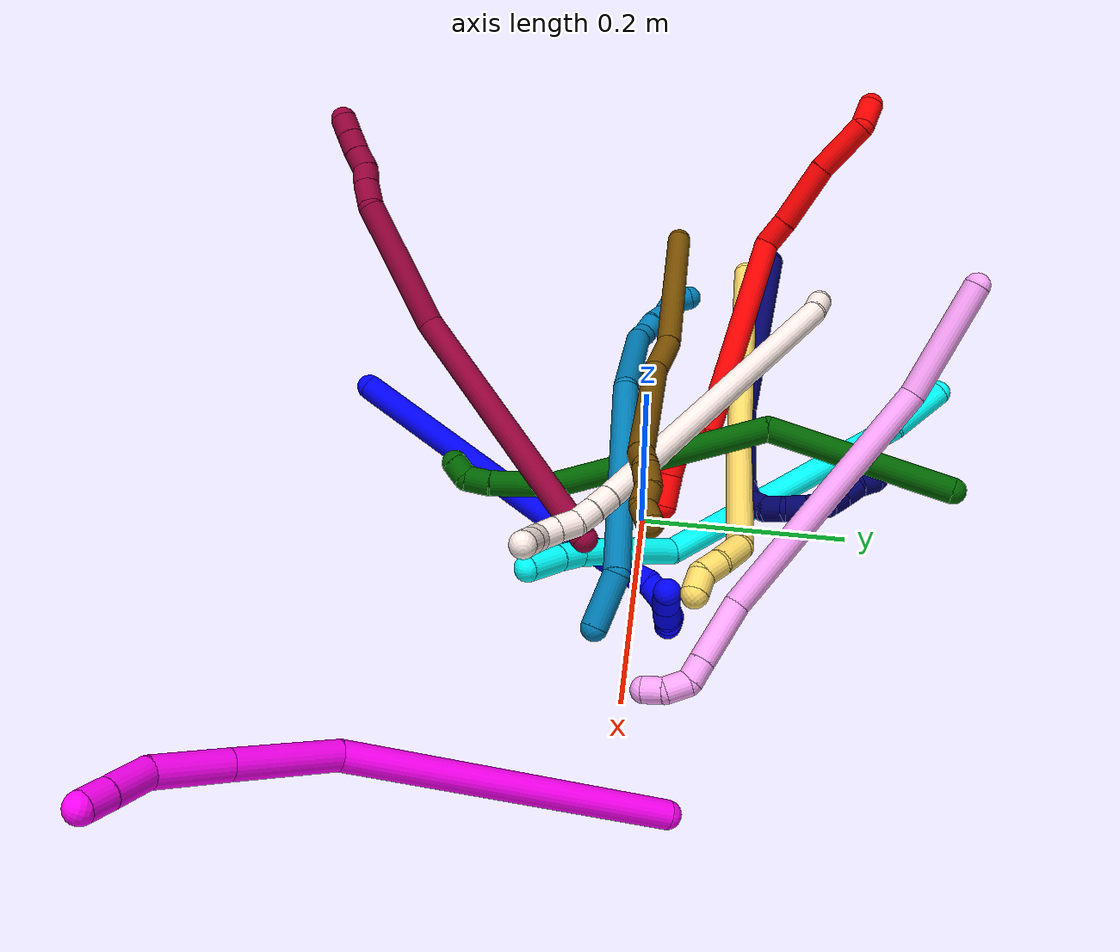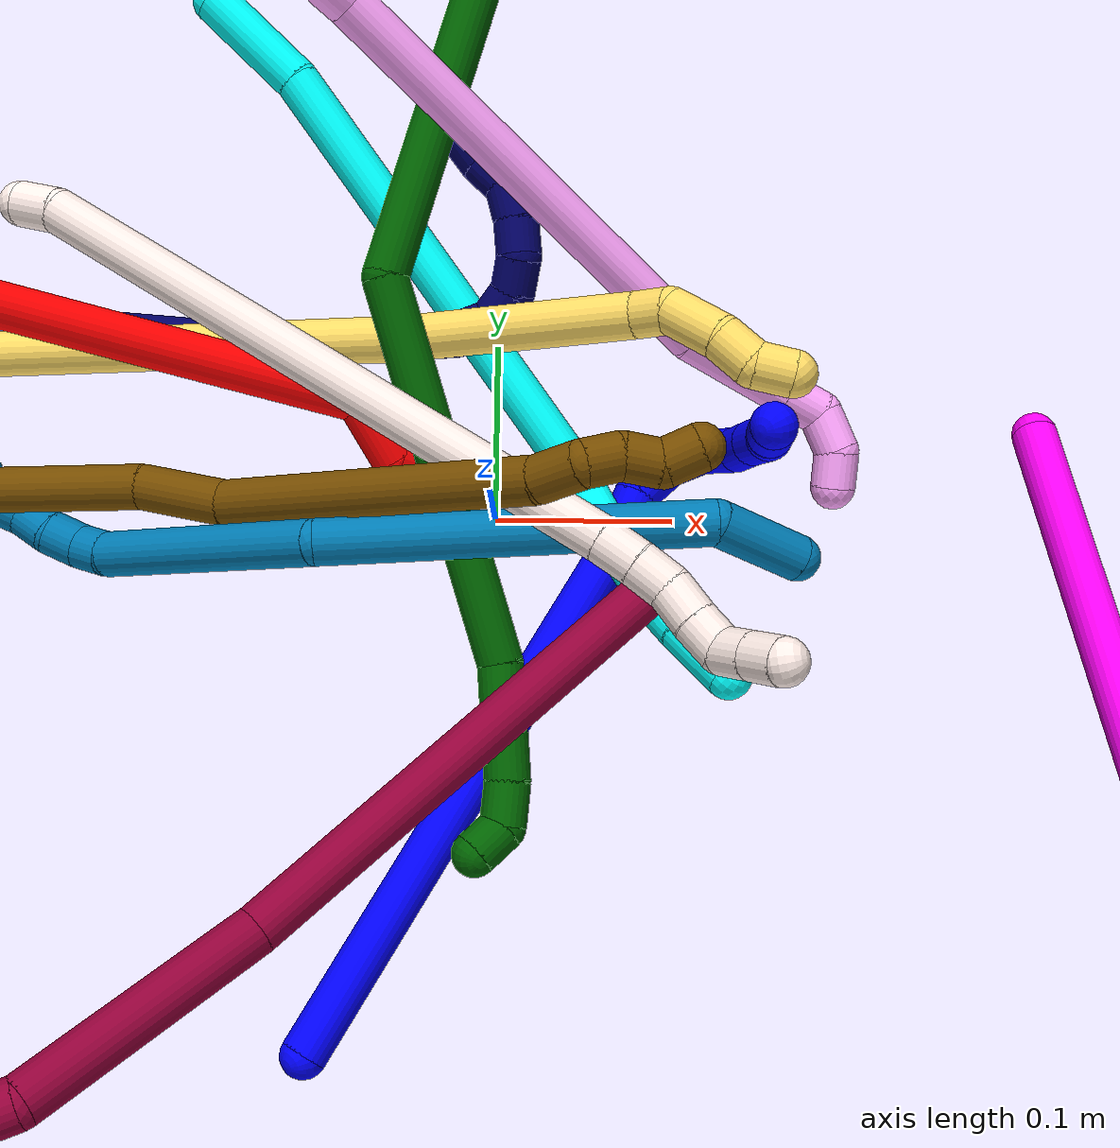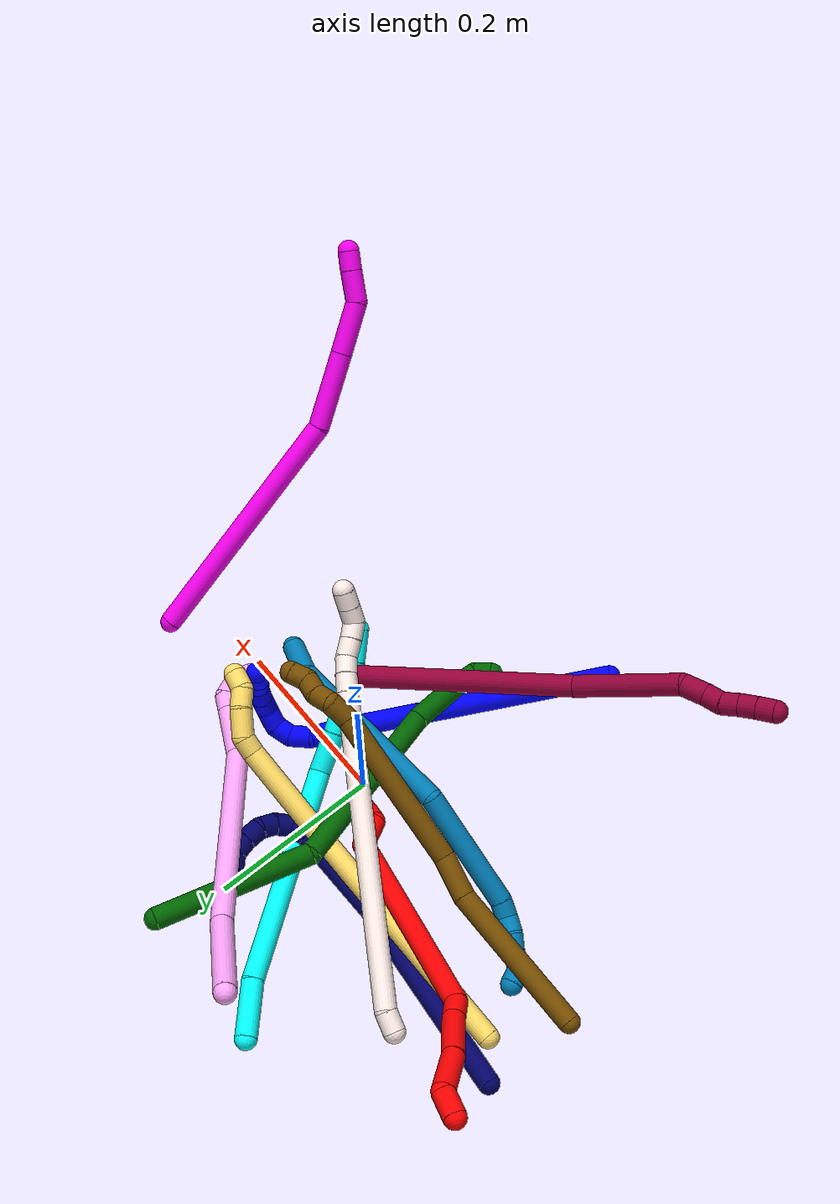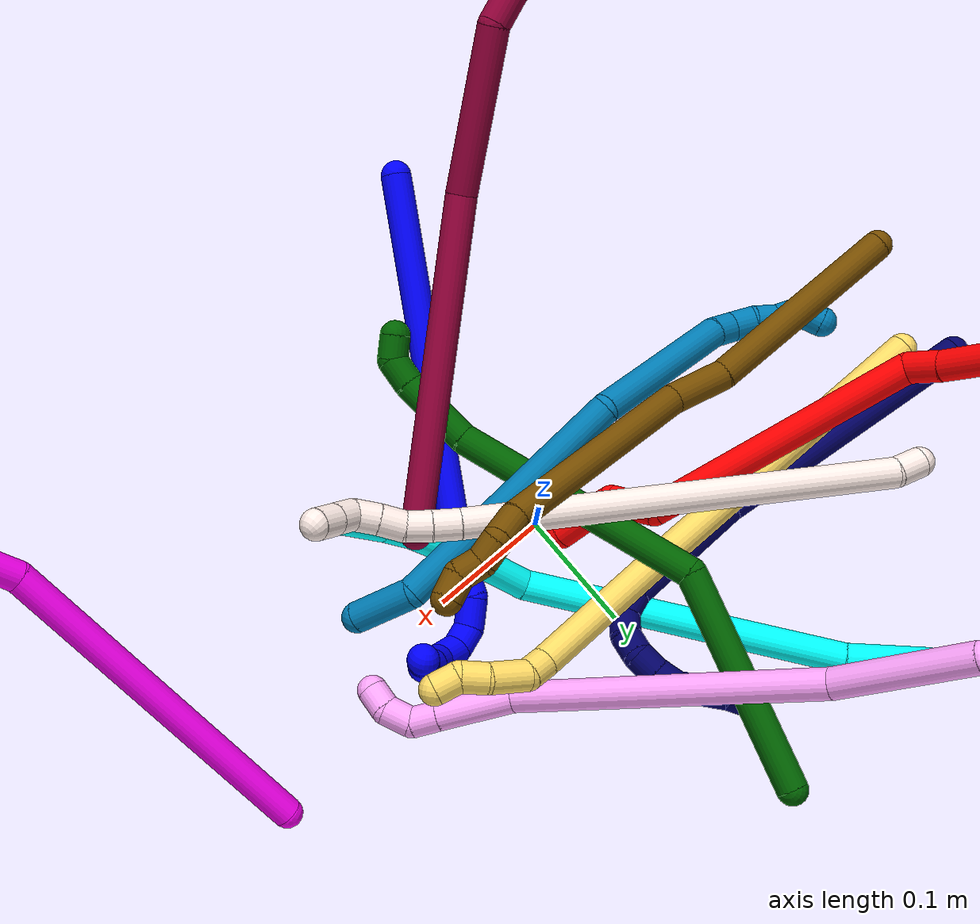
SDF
<sdf version="1.7">
 <world name="default">
  <plugin name="TubeGeneratorPlugin" filename="libtube_generator_plugin.so"/>
  <model name="photoneo_s_sensor">
   <static>1</static>
   <pose>0 0 2 1.57079 1.57079 3.14159</pose>
   <link name="link">
    <inertial><mass>0.1</mass></inertial>
    <sensor name="sensor" type="depth">
     <update_rate>30</update_rate>
     <camera>
      <horizontal_fov>1.22</horizontal_fov>
      <image><width>1920</width><height>1200</height><format>B8G8R8</format></image>
      <clip><near>0.1</near><far>4</far></clip>
      <depth_camera><output>points</output></depth_camera>
     </camera>
     <plugin name="camera_plugin" filename="libgazebo_ros_depth_camera.so">
      <baseline>0.2</baseline>
      <alwaysOn>1</alwaysOn>
      <updateRate>0.0</updateRate>
      <cameraName>camera_ir</cameraName>
      <imageTopicName>/camera/color/image_raw</imageTopicName>
      <cameraInfoTopicName>/camera/color/camera_info</cameraInfoTopicName>
      <depthImageTopicName>/camera/depth/image_raw</depthImageTopicName>
      <depthImageCameraInfoTopicName>/camera/depth/camera_info</depthImageCameraInfoTopicName>
      <pointCloudTopicName>/camera/depth/points</pointCloudTopicName>
      <frameName>fr_optical</frameName>
      <pointCloudCutoff>0.1</pointCloudCutoff>
      <pointCloudCutoffMax>2.0</pointCloudCutoffMax>
      <distortionK1>0</distortionK1>
      <distortionK2>0</distortionK2>
      <distortionK3>0</distortionK3>
      <distortionT1>0</distortionT1>
      <distortionT2>0</distortionT2>
      <CxPrime>0</CxPrime>
      <Cx>0</Cx>
      <Cy>0</Cy>
      <focalLength>0</focalLength>
      <hackBaseline>0</hackBaseline>
     </plugin>
    </sensor>
   </link>
  </model>
  <gravity>0 0 -9.8</gravity>
  <magnetic_field>6e-06 2.3e-05 -4.2e-05</magnetic_field>
  <atmosphere type="adiabatic"/>
  <physics name="default_physics" default="0" type="ode">
   <max_step_size>0.003</max_step_size>
   <real_time_factor>1</real_time_factor>
   <real_time_update_rate>1000</real_time_update_rate>
   <max_contacts>10000</max_contacts>
   <ode>
    <solver>
     <type>quick</type>
     <iters>100</iters>
     <sor>1.3</sor>
     <use_dynamic_moi_rescaling>0</use_dynamic_moi_rescaling>
    </solver>
    <constraints>
     <contact_max_correcting_vel>0</contact_max_correcting_vel>
     <contact_surface_layer>0.001</contact_surface_layer>
     <cfm>0</cfm>
     <erp>0.2</erp>
    </constraints>
   </ode>
  </physics>
  <scene><ambient>0.4 0.4 0.4 1</ambient><background>0.7 0.7 0.7 1</background><shadows>0</shadows></scene>
  <audio><device>default</device></audio>
  <spherical_coordinates>
   <surface_model>EARTH_WGS84</surface_model>
   <latitude_deg>0</latitude_deg>
   <longitude_deg>0</longitude_deg>
   <elevation>0</elevation>
   <heading_deg>0</heading_deg>
  </spherical_coordinates>
  <model name="bin">
   <static>1</static>
   <link name="bottom">
    <collision name="collision-bottom">
     <pose>0 0 -0.01 0 -0 0</pose>
     <geometry><box><size>0.8 0.6 0.02</size></box></geometry>
     <surface>
      <friction><ode><mu>100</mu><mu2>100</mu2></ode></friction>
      <contact><collide_bitmask>65535</collide_bitmask></contact>
     </surface>
    </collision>
   </link>
   <link name="west_wall">
    <collision name="collision-west_wall">
     <pose>-0.41 0 0.1 0 -0 0</pose>
     <geometry><box><size>0.02 0.6 0.2</size></box></geometry>
     <surface>
      <friction><ode><mu>100</mu><mu2>100</mu2></ode></friction>
      <contact><collide_bitmask>65535</collide_bitmask></contact>
     </surface>
    </collision>
   </link>
   <link name="east_wall">
    <collision name="collision-east_wall">
     <pose>0.41 0 0.1 0 -0 0</pose>
     <geometry><box><size>0.02 0.6 0.2</size></box></geometry>
     <surface>
      <friction><ode><mu>100</mu><mu2>100</mu2></ode></friction>
      <contact><collide_bitmask>65535</collide_bitmask></contact>
     </surface>
    </collision>
   </link>
   <link name="south_wall">
    <collision name="collision-south_wall">
     <pose>0 -0.31 0.1 0 -0 0</pose>
     <geometry><box><size>0.8 0.02 0.2</size></box></geometry>
     <surface>
      <friction><ode><mu>100</mu><mu2>100</mu2></ode></friction>
      <contact><collide_bitmask>65535</collide_bitmask></contact>
     </surface>
    </collision>
   </link>
   <link name="north_wall">
    <collision name="collision-north_wall">
     <pose>0 0.31 0.1 0 -0 0</pose>
     <geometry><box><size>0.8 0.02 0.2</size></box></geometry>
     <surface>
      <friction><ode><mu>100</mu><mu2>100</mu2></ode></friction>
      <contact><collide_bitmask>65535</collide_bitmask></contact>
     </surface>
    </collision>
   </link>
  </model>
  <model name="1">
   <static>0</static>
   <link name="1">
    <collision name="collision-cylinder-e_1_1_4">
     <pose>0.070733 0.076164 -0.121175 -2.58045 0.459004 -1.36244</pose>
     <geometry><cylinder><radius>0.0125</radius><length>0.319297</length></cylinder></geometry>
     <surface>
      <friction><ode><mu>1.16</mu><mu2>1.16</mu2><slip1>0</slip1><slip2>0</slip2></ode></friction>
      <contact><ode><kp>1e+06</kp><kd>1</kd><max_vel>0</max_vel><min_depth>0.001</min_depth></ode></contact>
     </surface>
    </collision>
    <visual name="visual-cylinder-e_1_1_4">
     <pose>0.070733 0.076164 -0.121175 -2.58045 0.459004 -1.36244</pose>
     <geometry><cylinder><radius>0.0125</radius><length>0.319297</length></cylinder></geometry>
     <material><ambient>0 0 1 1</ambient></material>
    </visual>
    <collision name="collision-cylinder-e_2_4_5">
     <pose>0.148908 0.162032 -0.252272 -2.36735 0.492259 -1.1045</pose>
     <geometry><cylinder><radius>0.0125</radius><length>0.031494</length></cylinder></geometry>
     <surface>
      <friction><ode><mu>1.16</mu><mu2>1.16</mu2><slip1>0</slip1><slip2>0</slip2></ode></friction>
      <contact><ode><kp>1e+06</kp><kd>1</kd><max_vel>0</max_vel><min_depth>0.001</min_depth></ode></contact>
     </surface>
    </collision>
    <visual name="visual-cylinder-e_2_4_5">
     <pose>0.148908 0.162032 -0.252272 -2.36735 0.492259 -1.1045</pose>
     <geometry><cylinder><radius>0.0125</radius><length>0.031494</length></cylinder></geometry>
     <material><ambient>0 0 1 1</ambient></material>
    </visual>
    <collision name="collision-cylinder-e_3_5_6">
     <pose>0.162961 0.174394 -0.272682 -2.89323 0.548386 -2.30627</pose>
     <geometry><cylinder><radius>0.0125</radius><length>0.02536</length></cylinder></geometry>
     <surface>
      <friction><ode><mu>1.16</mu><mu2>1.16</mu2><slip1>0</slip1><slip2>0</slip2></ode></friction>
      <contact><ode><kp>1e+06</kp><kd>1</kd><max_vel>0</max_vel><min_depth>0.001</min_depth></ode></contact>
     </surface>
    </collision>
    <visual name="visual-cylinder-e_3_5_6">
     <pose>0.162961 0.174394 -0.272682 -2.89323 0.548386 -2.30627</pose>
     <geometry><cylinder><radius>0.0125</radius><length>0.02536</length></cylinder></geometry>
     <material><ambient>0 0 1 1</ambient></material>
    </visual>
    <collision name="collision-cylinder-e_4_6_7">
     <pose>0.1779 0.17552 -0.288527 2.86272 0.981267 2.62775</pose>
     <geometry><cylinder><radius>0.0125</radius><length>0.020042</length></cylinder></geometry>
     <surface>
      <friction><ode><mu>1.16</mu><mu2>1.16</mu2><slip1>0</slip1><slip2>0</slip2></ode></friction>
      <contact><ode><kp>1e+06</kp><kd>1</kd><max_vel>0</max_vel><min_depth>0.001</min_depth></ode></contact>
     </surface>
    </collision>
    <visual name="visual-cylinder-e_4_6_7">
     <pose>0.1779 0.17552 -0.288527 2.86272 0.981267 2.62775</pose>
     <geometry><cylinder><radius>0.0125</radius><length>0.020042</length></cylinder></geometry>
     <material><ambient>0 0 1 1</ambient></material>
    </visual>
    <collision name="collision-cylinder-e_5_7_8">
     <pose>0.196778 0.169395 -0.294046 1.60625 1.16 1.19274</pose>
     <geometry><cylinder><radius>0.0125</radius><length>0.023011</length></cylinder></geometry>
     <surface>
      <friction><ode><mu>1.16</mu><mu2>1.16</mu2><slip1>0</slip1><slip2>0</slip2></ode></friction>
      <contact><ode><kp>1e+06</kp><kd>1</kd><max_vel>0</max_vel><min_depth>0.001</min_depth></ode></contact>
     </surface>
    </collision>
    <visual name="visual-cylinder-e_5_7_8">
     <pose>0.196778 0.169395 -0.294046 1.60625 1.16 1.19274</pose>
     <geometry><cylinder><radius>0.0125</radius><length>0.023011</length></cylinder></geometry>
     <material><ambient>0 0 1 1</ambient></material>
    </visual>
    <collision name="collision-cylinder-e_6_8_9">
     <pose>0.216645 0.163697 -0.290394 0.282203 1.16791 0.187189</pose>
     <geometry><cylinder><radius>0.0125</radius><length>0.020259</length></cylinder></geometry>
     <surface>
      <friction><ode><mu>1.16</mu><mu2>1.16</mu2><slip1>0</slip1><slip2>0</slip2></ode></friction>
      <contact><ode><kp>1e+06</kp><kd>1</kd><max_vel>0</max_vel><min_depth>0.001</min_depth></ode></contact>
     </surface>
    </collision>
    <visual name="visual-cylinder-e_6_8_9">
     <pose>0.216645 0.163697 -0.290394 0.282203 1.16791 0.187189</pose>
     <geometry><cylinder><radius>0.0125</radius><length>0.020259</length></cylinder></geometry>
     <material><ambient>0 0 1 1</ambient></material>
    </visual>
    <collision name="collision-cylinder-e_7_9_10">
     <pose>0.234927 0.161015 -0.282424 0.362489 1.11047 0.226387</pose>
     <geometry><cylinder><radius>0.0125</radius><length>0.02001</length></cylinder></geometry>
     <surface>
      <friction><ode><mu>1.16</mu><mu2>1.16</mu2><slip1>0</slip1><slip2>0</slip2></ode></friction>
      <contact><ode><kp>1e+06</kp><kd>1</kd><max_vel>0</max_vel><min_depth>0.001</min_depth></ode></contact>
     </surface>
    </collision>
    <visual name="visual-cylinder-e_7_9_10">
     <pose>0.234927 0.161015 -0.282424 0.362489 1.11047 0.226387</pose>
     <geometry><cylinder><radius>0.0125</radius><length>0.02001</length></cylinder></geometry>
     <material><ambient>0 0 1 1</ambient></material>
    </visual>
    <collision name="collision-cylinder-e_8_10_11">
     <pose>0.250617 0.159558 -0.27075 -0.015859 0.729801 -0.006058</pose>
     <geometry><cylinder><radius>0.0125</radius><length>0.020177</length></cylinder></geometry>
     <surface>
      <friction><ode><mu>1.16</mu><mu2>1.16</mu2><slip1>0</slip1><slip2>0</slip2></ode></friction>
      <contact><ode><kp>1e+06</kp><kd>1</kd><max_vel>0</max_vel><min_depth>0.001</min_depth></ode></contact>
     </surface>
    </collision>
    <visual name="visual-cylinder-e_8_10_11">
     <pose>0.250617 0.159558 -0.27075 -0.015859 0.729801 -0.006058</pose>
     <geometry><cylinder><radius>0.0125</radius><length>0.020177</length></cylinder></geometry>
     <material><ambient>0 0 1 1</ambient></material>
    </visual>
    <collision name="collision-cylinder-e_9_11_2">
     <pose>0.264999 0.160468 -0.256576 -0.118261 0.851722 -0.053695</pose>
     <geometry><cylinder><radius>0.0125</radius><length>0.020351</length></cylinder></geometry>
     <surface>
      <friction><ode><mu>1.16</mu><mu2>1.16</mu2><slip1>0</slip1><slip2>0</slip2></ode></friction>
      <contact><ode><kp>1e+06</kp><kd>1</kd><max_vel>0</max_vel><min_depth>0.001</min_depth></ode></contact>
     </surface>
    </collision>
    <visual name="visual-cylinder-e_9_11_2">
     <pose>0.264999 0.160468 -0.256576 -0.118261 0.851722 -0.053695</pose>
     <geometry><cylinder><radius>0.0125</radius><length>0.020351</length></cylinder></geometry>
     <material><ambient>0 0 1 1</ambient></material>
    </visual>
    <collision name="collision-sphere-2">
     <pose>0.272655 0.161259 -0.249921 0 -0 0</pose>
     <geometry><sphere><radius>0.0125</radius></sphere></geometry>
     <surface>
      <friction><ode><mu>1.16</mu><mu2>1.16</mu2><slip1>0</slip1><slip2>0</slip2></ode></friction>
      <contact><ode><kp>1e+06</kp><kd>1</kd><max_vel>0</max_vel><min_depth>0.001</min_depth></ode></contact>
     </surface>
    </collision>
    <visual name="visual-sphere-2">
     <pose>0.272655 0.161259 -0.249921 0 -0 0</pose>
     <geometry><sphere><radius>0.0125</radius></sphere></geometry>
     <material><ambient>0 0 1 1</ambient></material>
    </visual>
    <collision name="collision-sphere-11">
     <pose>0.257343 0.159678 -0.263232 0 -0 0</pose>
     <geometry><sphere><radius>0.0125</radius></sphere></geometry>
     <surface>
      <friction><ode><mu>1.16</mu><mu2>1.16</mu2><slip1>0</slip1><slip2>0</slip2></ode></friction>
      <contact><ode><kp>1e+06</kp><kd>1</kd><max_vel>0</max_vel><min_depth>0.001</min_depth></ode></contact>
     </surface>
    </collision>
    <visual name="visual-sphere-11">
     <pose>0.257343 0.159678 -0.263232 0 -0 0</pose>
     <geometry><sphere><radius>0.0125</radius></sphere></geometry>
     <material><ambient>0 0 1 1</ambient></material>
    </visual>
    <collision name="collision-sphere-10">
     <pose>0.243891 0.159439 -0.278268 0 -0 0</pose>
     <geometry><sphere><radius>0.0125</radius></sphere></geometry>
     <surface>
      <friction><ode><mu>1.16</mu><mu2>1.16</mu2><slip1>0</slip1><slip2>0</slip2></ode></friction>
      <contact><ode><kp>1e+06</kp><kd>1</kd><max_vel>0</max_vel><min_depth>0.001</min_depth></ode></contact>
     </surface>
    </collision>
    <visual name="visual-sphere-10">
     <pose>0.243891 0.159439 -0.278268 0 -0 0</pose>
     <geometry><sphere><radius>0.0125</radius></sphere></geometry>
     <material><ambient>0 0 1 1</ambient></material>
    </visual>
    <collision name="collision-sphere-9">
     <pose>0.225963 0.162591 -0.28658 0 -0 0</pose>
     <geometry><sphere><radius>0.0125</radius></sphere></geometry>
     <surface>
      <friction><ode><mu>1.16</mu><mu2>1.16</mu2><slip1>0</slip1><slip2>0</slip2></ode></friction>
      <contact><ode><kp>1e+06</kp><kd>1</kd><max_vel>0</max_vel><min_depth>0.001</min_depth></ode></contact>
     </surface>
    </collision>
    <visual name="visual-sphere-9">
     <pose>0.225963 0.162591 -0.28658 0 -0 0</pose>
     <geometry><sphere><radius>0.0125</radius></sphere></geometry>
     <material><ambient>0 0 1 1</ambient></material>
    </visual>
    <collision name="collision-sphere-4">
     <pose>0.141466 0.152329 -0.24235 0 -0 0</pose>
     <geometry><sphere><radius>0.0125</radius></sphere></geometry>
     <surface>
      <friction><ode><mu>1.16</mu><mu2>1.16</mu2><slip1>0</slip1><slip2>0</slip2></ode></friction>
      <contact><ode><kp>1e+06</kp><kd>1</kd><max_vel>0</max_vel><min_depth>0.001</min_depth></ode></contact>
     </surface>
    </collision>
    <visual name="visual-sphere-4">
     <pose>0.141466 0.152329 -0.24235 0 -0 0</pose>
     <geometry><sphere><radius>0.0125</radius></sphere></geometry>
     <material><ambient>0 0 1 1</ambient></material>
    </visual>
    <collision name="collision-sphere-1">
     <geometry><sphere><radius>0.0125</radius></sphere></geometry>
     <surface>
      <friction><ode><mu>1.16</mu><mu2>1.16</mu2><slip1>0</slip1><slip2>0</slip2></ode></friction>
      <contact><ode><kp>1e+06</kp><kd>1</kd><max_vel>0</max_vel><min_depth>0.001</min_depth></ode></contact>
     </surface>
    </collision>
    <visual name="visual-sphere-1">
     <geometry><sphere><radius>0.0125</radius></sphere></geometry>
     <material><ambient>0 0 1 1</ambient></material>
    </visual>
    <collision name="collision-sphere-8">
     <pose>0.207326 0.164803 -0.294208 0 -0 0</pose>
     <geometry><sphere><radius>0.0125</radius></sphere></geometry>
     <surface>
      <friction><ode><mu>1.16</mu><mu2>1.16</mu2><slip1>0</slip1><slip2>0</slip2></ode></friction>
      <contact><ode><kp>1e+06</kp><kd>1</kd><max_vel>0</max_vel><min_depth>0.001</min_depth></ode></contact>
     </surface>
    </collision>
    <visual name="visual-sphere-8">
     <pose>0.207326 0.164803 -0.294208 0 -0 0</pose>
     <geometry><sphere><radius>0.0125</radius></sphere></geometry>
     <material><ambient>0 0 1 1</ambient></material>
    </visual>
    <collision name="collision-sphere-5">
     <pose>0.156351 0.171734 -0.262193 0 -0 0</pose>
     <geometry><sphere><radius>0.0125</radius></sphere></geometry>
     <surface>
      <friction><ode><mu>1.16</mu><mu2>1.16</mu2><slip1>0</slip1><slip2>0</slip2></ode></friction>
      <contact><ode><kp>1e+06</kp><kd>1</kd><max_vel>0</max_vel><min_depth>0.001</min_depth></ode></contact>
     </surface>
    </collision>
    <visual name="visual-sphere-5">
     <pose>0.156351 0.171734 -0.262193 0 -0 0</pose>
     <geometry><sphere><radius>0.0125</radius></sphere></geometry>
     <material><ambient>0 0 1 1</ambient></material>
    </visual>
    <collision name="collision-sphere-6">
     <pose>0.169571 0.177054 -0.283171 0 -0 0</pose>
     <geometry><sphere><radius>0.0125</radius></sphere></geometry>
     <surface>
      <friction><ode><mu>1.16</mu><mu2>1.16</mu2><slip1>0</slip1><slip2>0</slip2></ode></friction>
      <contact><ode><kp>1e+06</kp><kd>1</kd><max_vel>0</max_vel><min_depth>0.001</min_depth></ode></contact>
     </surface>
    </collision>
    <visual name="visual-sphere-6">
     <pose>0.169571 0.177054 -0.283171 0 -0 0</pose>
     <geometry><sphere><radius>0.0125</radius></sphere></geometry>
     <material><ambient>0 0 1 1</ambient></material>
    </visual>
    <collision name="collision-sphere-7">
     <pose>0.18623 0.173987 -0.293883 0 -0 0</pose>
     <geometry><sphere><radius>0.0125</radius></sphere></geometry>
     <surface>
      <friction><ode><mu>1.16</mu><mu2>1.16</mu2><slip1>0</slip1><slip2>0</slip2></ode></friction>
      <contact><ode><kp>1e+06</kp><kd>1</kd><max_vel>0</max_vel><min_depth>0.001</min_depth></ode></contact>
     </surface>
    </collision>
    <visual name="visual-sphere-7">
     <pose>0.18623 0.173987 -0.293883 0 -0 0</pose>
     <geometry><sphere><radius>0.0125</radius></sphere></geometry>
     <material><ambient>0 0 1 1</ambient></material>
    </visual>
    <inertial>
     <pose>0.11808 0.108567 -0.176637 0 -0 0</pose>
     <mass>0.5</mass>
     <inertia>
      <ixx>-0.001864</ixx>
      <ixy>0</ixy>
      <ixz>0</ixz>
      <iyy>-0.002219</iyy>
      <iyz>0</iyz>
      <izz>-0.002539</izz>
     </inertia>
    </inertial>
   </link>
   <pose>-0.092999 -0.288503 0.055786 0.087195 -0.863797 0.461577</pose>
  </model>
  <model name="2">
   <static>0</static>
   <link name="2">
    <collision name="collision-cylinder-e_1_1_4">
     <pose>0.001347 -0.001269 -0.014573 3.05475 0.091822 1.62663</pose>
     <geometry><cylinder><radius>0.0125</radius><length>0.029379</length></cylinder></geometry>
     <surface>
      <friction><ode><mu>1.16</mu><mu2>1.16</mu2><slip1>0</slip1><slip2>0</slip2></ode></friction>
      <contact><ode><kp>1e+06</kp><kd>1</kd><max_vel>0</max_vel><min_depth>0.001</min_depth></ode></contact>
     </surface>
    </collision>
    <visual name="visual-cylinder-e_1_1_4">
     <pose>0.001347 -0.001269 -0.014573 3.05475 0.091822 1.62663</pose>
     <geometry><cylinder><radius>0.0125</radius><length>0.029379</length></cylinder></geometry>
     <material><ambient>1 0 0 1</ambient></material>
    </visual>
    <collision name="collision-cylinder-e_2_4_5">
     <pose>0.004822 0.014902 -0.052022 -2.49025 0.073847 -0.217913</pose>
     <geometry><cylinder><radius>0.0125</radius><length>0.057687</length></cylinder></geometry>
     <surface>
      <friction><ode><mu>1.16</mu><mu2>1.16</mu2><slip1>0</slip1><slip2>0</slip2></ode></friction>
      <contact><ode><kp>1e+06</kp><kd>1</kd><max_vel>0</max_vel><min_depth>0.001</min_depth></ode></contact>
     </surface>
    </collision>
    <visual name="visual-cylinder-e_2_4_5">
     <pose>0.004822 0.014902 -0.052022 -2.49025 0.073847 -0.217913</pose>
     <geometry><cylinder><radius>0.0125</radius><length>0.057687</length></cylinder></geometry>
     <material><ambient>1 0 0 1</ambient></material>
    </visual>
    <collision name="collision-cylinder-e_3_5_6">
     <pose>0.01396 0.049352 -0.102584 -2.59061 0.212474 -0.721476</pose>
     <geometry><cylinder><radius>0.0125</radius><length>0.066486</length></cylinder></geometry>
     <surface>
      <friction><ode><mu>1.16</mu><mu2>1.16</mu2><slip1>0</slip1><slip2>0</slip2></ode></friction>
      <contact><ode><kp>1e+06</kp><kd>1</kd><max_vel>0</max_vel><min_depth>0.001</min_depth></ode></contact>
     </surface>
    </collision>
    <visual name="visual-cylinder-e_3_5_6">
     <pose>0.01396 0.049352 -0.102584 -2.59061 0.212474 -0.721476</pose>
     <geometry><cylinder><radius>0.0125</radius><length>0.066486</length></cylinder></geometry>
     <material><ambient>1 0 0 1</ambient></material>
    </visual>
    <collision name="collision-cylinder-e_4_6_7">
     <pose>0.022993 0.074593 -0.142368 -2.54429 0.137379 -0.439716</pose>
     <geometry><cylinder><radius>0.0125</radius><length>0.029541</length></cylinder></geometry>
     <surface>
      <friction><ode><mu>1.16</mu><mu2>1.16</mu2><slip1>0</slip1><slip2>0</slip2></ode></friction>
      <contact><ode><kp>1e+06</kp><kd>1</kd><max_vel>0</max_vel><min_depth>0.001</min_depth></ode></contact>
     </surface>
    </collision>
    <visual name="visual-cylinder-e_4_6_7">
     <pose>0.022993 0.074593 -0.142368 -2.54429 0.137379 -0.439716</pose>
     <geometry><cylinder><radius>0.0125</radius><length>0.029541</length></cylinder></geometry>
     <material><ambient>1 0 0 1</ambient></material>
    </visual>
    <collision name="collision-cylinder-e_5_7_8">
     <pose>0.04503 0.071914 -0.264981 3.04322 0.178311 2.13483</pose>
     <geometry><cylinder><radius>0.0125</radius><length>0.225682</length></cylinder></geometry>
     <surface>
      <friction><ode><mu>1.16</mu><mu2>1.16</mu2><slip1>0</slip1><slip2>0</slip2></ode></friction>
      <contact><ode><kp>1e+06</kp><kd>1</kd><max_vel>0</max_vel><min_depth>0.001</min_depth></ode></contact>
     </surface>
    </collision>
    <visual name="visual-cylinder-e_5_7_8">
     <pose>0.04503 0.071914 -0.264981 3.04322 0.178311 2.13483</pose>
     <geometry><cylinder><radius>0.0125</radius><length>0.225682</length></cylinder></geometry>
     <material><ambient>1 0 0 1</ambient></material>
    </visual>
    <collision name="collision-cylinder-e_6_8_9">
     <pose>0.061477 0.071331 -0.390849 -2.54963 -0.190466 0.607138</pose>
     <geometry><cylinder><radius>0.0125</radius><length>0.037684</length></cylinder></geometry>
     <surface>
      <friction><ode><mu>1.16</mu><mu2>1.16</mu2><slip1>0</slip1><slip2>0</slip2></ode></friction>
      <contact><ode><kp>1e+06</kp><kd>1</kd><max_vel>0</max_vel><min_depth>0.001</min_depth></ode></contact>
     </surface>
    </collision>
    <visual name="visual-cylinder-e_6_8_9">
     <pose>0.061477 0.071331 -0.390849 -2.54963 -0.190466 0.607138</pose>
     <geometry><cylinder><radius>0.0125</radius><length>0.037684</length></cylinder></geometry>
     <material><ambient>1 0 0 1</ambient></material>
    </visual>
    <collision name="collision-cylinder-e_7_9_10">
     <pose>0.062164 0.083434 -0.415818 -2.95854 0.410242 -2.31065</pose>
     <geometry><cylinder><radius>0.0125</radius><length>0.021329</length></cylinder></geometry>
     <surface>
      <friction><ode><mu>1.16</mu><mu2>1.16</mu2><slip1>0</slip1><slip2>0</slip2></ode></friction>
      <contact><ode><kp>1e+06</kp><kd>1</kd><max_vel>0</max_vel><min_depth>0.001</min_depth></ode></contact>
     </surface>
    </collision>
    <visual name="visual-cylinder-e_7_9_10">
     <pose>0.062164 0.083434 -0.415818 -2.95854 0.410242 -2.31065</pose>
     <geometry><cylinder><radius>0.0125</radius><length>0.021329</length></cylinder></geometry>
     <material><ambient>1 0 0 1</ambient></material>
    </visual>
    <collision name="collision-cylinder-e_8_10_2">
     <pose>0.072846 0.086055 -0.440178 -3.08464 0.410616 -2.8697</pose>
     <geometry><cylinder><radius>0.0125</radius><length>0.032213</length></cylinder></geometry>
     <surface>
      <friction><ode><mu>1.16</mu><mu2>1.16</mu2><slip1>0</slip1><slip2>0</slip2></ode></friction>
      <contact><ode><kp>1e+06</kp><kd>1</kd><max_vel>0</max_vel><min_depth>0.001</min_depth></ode></contact>
     </surface>
    </collision>
    <visual name="visual-cylinder-e_8_10_2">
     <pose>0.072846 0.086055 -0.440178 -3.08464 0.410616 -2.8697</pose>
     <geometry><cylinder><radius>0.0125</radius><length>0.032213</length></cylinder></geometry>
     <material><ambient>1 0 0 1</ambient></material>
    </visual>
    <collision name="collision-sphere-2">
     <pose>0.079276 0.086896 -0.454921 0 -0 0</pose>
     <geometry><sphere><radius>0.0125</radius></sphere></geometry>
     <surface>
      <friction><ode><mu>1.16</mu><mu2>1.16</mu2><slip1>0</slip1><slip2>0</slip2></ode></friction>
      <contact><ode><kp>1e+06</kp><kd>1</kd><max_vel>0</max_vel><min_depth>0.001</min_depth></ode></contact>
     </surface>
    </collision>
    <visual name="visual-sphere-2">
     <pose>0.079276 0.086896 -0.454921 0 -0 0</pose>
     <geometry><sphere><radius>0.0125</radius></sphere></geometry>
     <material><ambient>1 0 0 1</ambient></material>
    </visual>
    <collision name="collision-sphere-10">
     <pose>0.066417 0.085214 -0.425434 0 -0 0</pose>
     <geometry><sphere><radius>0.0125</radius></sphere></geometry>
     <surface>
      <friction><ode><mu>1.16</mu><mu2>1.16</mu2><slip1>0</slip1><slip2>0</slip2></ode></friction>
      <contact><ode><kp>1e+06</kp><kd>1</kd><max_vel>0</max_vel><min_depth>0.001</min_depth></ode></contact>
     </surface>
    </collision>
    <visual name="visual-sphere-10">
     <pose>0.066417 0.085214 -0.425434 0 -0 0</pose>
     <geometry><sphere><radius>0.0125</radius></sphere></geometry>
     <material><ambient>1 0 0 1</ambient></material>
    </visual>
    <collision name="collision-sphere-9">
     <pose>0.05791 0.081654 -0.406202 0 -0 0</pose>
     <geometry><sphere><radius>0.0125</radius></sphere></geometry>
     <surface>
      <friction><ode><mu>1.16</mu><mu2>1.16</mu2><slip1>0</slip1><slip2>0</slip2></ode></friction>
      <contact><ode><kp>1e+06</kp><kd>1</kd><max_vel>0</max_vel><min_depth>0.001</min_depth></ode></contact>
     </surface>
    </collision>
    <visual name="visual-sphere-9">
     <pose>0.05791 0.081654 -0.406202 0 -0 0</pose>
     <geometry><sphere><radius>0.0125</radius></sphere></geometry>
     <material><ambient>1 0 0 1</ambient></material>
    </visual>
    <collision name="collision-sphere-4">
     <pose>0.002694 -0.002537 -0.029145 0 -0 0</pose>
     <geometry><sphere><radius>0.0125</radius></sphere></geometry>
     <surface>
      <friction><ode><mu>1.16</mu><mu2>1.16</mu2><slip1>0</slip1><slip2>0</slip2></ode></friction>
      <contact><ode><kp>1e+06</kp><kd>1</kd><max_vel>0</max_vel><min_depth>0.001</min_depth></ode></contact>
     </surface>
    </collision>
    <visual name="visual-sphere-4">
     <pose>0.002694 -0.002537 -0.029145 0 -0 0</pose>
     <geometry><sphere><radius>0.0125</radius></sphere></geometry>
     <material><ambient>1 0 0 1</ambient></material>
    </visual>
    <collision name="collision-sphere-1">
     <geometry><sphere><radius>0.0125</radius></sphere></geometry>
     <surface>
      <friction><ode><mu>1.16</mu><mu2>1.16</mu2><slip1>0</slip1><slip2>0</slip2></ode></friction>
      <contact><ode><kp>1e+06</kp><kd>1</kd><max_vel>0</max_vel><min_depth>0.001</min_depth></ode></contact>
     </surface>
    </collision>
    <visual name="visual-sphere-1">
     <geometry><sphere><radius>0.0125</radius></sphere></geometry>
     <material><ambient>1 0 0 1</ambient></material>
    </visual>
    <collision name="collision-sphere-8">
     <pose>0.065045 0.061007 -0.375495 0 -0 0</pose>
     <geometry><sphere><radius>0.0125</radius></sphere></geometry>
     <surface>
      <friction><ode><mu>1.16</mu><mu2>1.16</mu2><slip1>0</slip1><slip2>0</slip2></ode></friction>
      <contact><ode><kp>1e+06</kp><kd>1</kd><max_vel>0</max_vel><min_depth>0.001</min_depth></ode></contact>
     </surface>
    </collision>
    <visual name="visual-sphere-8">
     <pose>0.065045 0.061007 -0.375495 0 -0 0</pose>
     <geometry><sphere><radius>0.0125</radius></sphere></geometry>
     <material><ambient>1 0 0 1</ambient></material>
    </visual>
    <collision name="collision-sphere-5">
     <pose>0.00695 0.03234 -0.074898 0 -0 0</pose>
     <geometry><sphere><radius>0.0125</radius></sphere></geometry>
     <surface>
      <friction><ode><mu>1.16</mu><mu2>1.16</mu2><slip1>0</slip1><slip2>0</slip2></ode></friction>
      <contact><ode><kp>1e+06</kp><kd>1</kd><max_vel>0</max_vel><min_depth>0.001</min_depth></ode></contact>
     </surface>
    </collision>
    <visual name="visual-sphere-5">
     <pose>0.00695 0.03234 -0.074898 0 -0 0</pose>
     <geometry><sphere><radius>0.0125</radius></sphere></geometry>
     <material><ambient>1 0 0 1</ambient></material>
    </visual>
    <collision name="collision-sphere-6">
     <pose>0.02097 0.066364 -0.13027 0 -0 0</pose>
     <geometry><sphere><radius>0.0125</radius></sphere></geometry>
     <surface>
      <friction><ode><mu>1.16</mu><mu2>1.16</mu2><slip1>0</slip1><slip2>0</slip2></ode></friction>
      <contact><ode><kp>1e+06</kp><kd>1</kd><max_vel>0</max_vel><min_depth>0.001</min_depth></ode></contact>
     </surface>
    </collision>
    <visual name="visual-sphere-6">
     <pose>0.02097 0.066364 -0.13027 0 -0 0</pose>
     <geometry><sphere><radius>0.0125</radius></sphere></geometry>
     <material><ambient>1 0 0 1</ambient></material>
    </visual>
    <collision name="collision-sphere-7">
     <pose>0.025016 0.082822 -0.154466 0 -0 0</pose>
     <geometry><sphere><radius>0.0125</radius></sphere></geometry>
     <surface>
      <friction><ode><mu>1.16</mu><mu2>1.16</mu2><slip1>0</slip1><slip2>0</slip2></ode></friction>
      <contact><ode><kp>1e+06</kp><kd>1</kd><max_vel>0</max_vel><min_depth>0.001</min_depth></ode></contact>
     </surface>
    </collision>
    <visual name="visual-sphere-7">
     <pose>0.025016 0.082822 -0.154466 0 -0 0</pose>
     <geometry><sphere><radius>0.0125</radius></sphere></geometry>
     <material><ambient>1 0 0 1</ambient></material>
    </visual>
    <inertial>
     <pose>0.036154 0.059553 -0.224067 0 -0 0</pose>
     <mass>0.5</mass>
     <inertia>
      <ixx>0.000324</ixx>
      <ixy>0</ixy>
      <ixz>0</ixz>
      <iyy>0.001291</iyy>
      <iyz>0</iyz>
      <izz>-0.000153</izz>
     </inertia>
    </inertial>
   </link>
   <pose>-0.398435 0.194143 0.211415 -1.30404 0.787754 1.35926</pose>
  </model>
  <model name="3">
   <static>0</static>
   <link name="3">
    <collision name="collision-cylinder-e_1_1_4">
     <pose>0.031587 -0.00819 -0.002259 1.83995 1.30806 1.57745</pose>
     <geometry><cylinder><radius>0.0125</radius><length>0.065418</length></cylinder></geometry>
     <surface>
      <friction><ode><mu>1.16</mu><mu2>1.16</mu2><slip1>0</slip1><slip2>0</slip2></ode></friction>
      <contact><ode><kp>1e+06</kp><kd>1</kd><max_vel>0</max_vel><min_depth>0.001</min_depth></ode></contact>
     </surface>
    </collision>
    <visual name="visual-cylinder-e_1_1_4">
     <pose>0.031587 -0.00819 -0.002259 1.83995 1.30806 1.57745</pose>
     <geometry><cylinder><radius>0.0125</radius><length>0.065418</length></cylinder></geometry>
     <material><ambient>0.003922 1 0.996078 1</ambient></material>
    </visual>
    <collision name="collision-cylinder-e_2_4_5">
     <pose>0.184734 -0.055429 -0.036492 2.25689 1.17727 1.90742</pose>
     <geometry><cylinder><radius>0.0125</radius><length>0.263243</length></cylinder></geometry>
     <surface>
      <friction><ode><mu>1.16</mu><mu2>1.16</mu2><slip1>0</slip1><slip2>0</slip2></ode></friction>
      <contact><ode><kp>1e+06</kp><kd>1</kd><max_vel>0</max_vel><min_depth>0.001</min_depth></ode></contact>
     </surface>
    </collision>
    <visual name="visual-cylinder-e_2_4_5">
     <pose>0.184734 -0.055429 -0.036492 2.25689 1.17727 1.90742</pose>
     <geometry><cylinder><radius>0.0125</radius><length>0.263243</length></cylinder></geometry>
     <material><ambient>0.003922 1 0.996078 1</ambient></material>
    </visual>
    <collision name="collision-cylinder-e_3_5_6">
     <pose>0.321094 -0.114647 -0.068887 1.59169 0.632976 0.645438</pose>
     <geometry><cylinder><radius>0.0125</radius><length>0.050037</length></cylinder></geometry>
     <surface>
      <friction><ode><mu>1.16</mu><mu2>1.16</mu2><slip1>0</slip1><slip2>0</slip2></ode></friction>
      <contact><ode><kp>1e+06</kp><kd>1</kd><max_vel>0</max_vel><min_depth>0.001</min_depth></ode></contact>
     </surface>
    </collision>
    <visual name="visual-cylinder-e_3_5_6">
     <pose>0.321094 -0.114647 -0.068887 1.59169 0.632976 0.645438</pose>
     <geometry><cylinder><radius>0.0125</radius><length>0.050037</length></cylinder></geometry>
     <material><ambient>0.003922 1 0.996078 1</ambient></material>
    </visual>
    <collision name="collision-cylinder-e_4_6_7">
     <pose>0.355429 -0.157884 -0.068773 1.5476 0.702489 0.687633</pose>
     <geometry><cylinder><radius>0.0125</radius><length>0.060469</length></cylinder></geometry>
     <surface>
      <friction><ode><mu>1.16</mu><mu2>1.16</mu2><slip1>0</slip1><slip2>0</slip2></ode></friction>
      <contact><ode><kp>1e+06</kp><kd>1</kd><max_vel>0</max_vel><min_depth>0.001</min_depth></ode></contact>
     </surface>
    </collision>
    <visual name="visual-cylinder-e_4_6_7">
     <pose>0.355429 -0.157884 -0.068773 1.5476 0.702489 0.687633</pose>
     <geometry><cylinder><radius>0.0125</radius><length>0.060469</length></cylinder></geometry>
     <material><ambient>0.003922 1 0.996078 1</ambient></material>
    </visual>
    <collision name="collision-cylinder-e_5_7_8">
     <pose>0.383493 -0.189018 -0.067125 1.43365 0.808691 0.713892</pose>
     <geometry><cylinder><radius>0.0125</radius><length>0.023582</length></cylinder></geometry>
     <surface>
      <friction><ode><mu>1.16</mu><mu2>1.16</mu2><slip1>0</slip1><slip2>0</slip2></ode></friction>
      <contact><ode><kp>1e+06</kp><kd>1</kd><max_vel>0</max_vel><min_depth>0.001</min_depth></ode></contact>
     </surface>
    </collision>
    <visual name="visual-cylinder-e_5_7_8">
     <pose>0.383493 -0.189018 -0.067125 1.43365 0.808691 0.713892</pose>
     <geometry><cylinder><radius>0.0125</radius><length>0.023582</length></cylinder></geometry>
     <material><ambient>0.003922 1 0.996078 1</ambient></material>
    </visual>
    <collision name="collision-cylinder-e_6_8_2">
     <pose>0.406178 -0.208929 -0.06352 1.36345 0.863304 0.715443</pose>
     <geometry><cylinder><radius>0.0125</radius><length>0.037251</length></cylinder></geometry>
     <surface>
      <friction><ode><mu>1.16</mu><mu2>1.16</mu2><slip1>0</slip1><slip2>0</slip2></ode></friction>
      <contact><ode><kp>1e+06</kp><kd>1</kd><max_vel>0</max_vel><min_depth>0.001</min_depth></ode></contact>
     </surface>
    </collision>
    <visual name="visual-cylinder-e_6_8_2">
     <pose>0.406178 -0.208929 -0.06352 1.36345 0.863304 0.715443</pose>
     <geometry><cylinder><radius>0.0125</radius><length>0.037251</length></cylinder></geometry>
     <material><ambient>0.003922 1 0.996078 1</ambient></material>
    </visual>
    <collision name="collision-sphere-2">
     <pose>0.420333 -0.220775 -0.061028 0 -0 0</pose>
     <geometry><sphere><radius>0.0125</radius></sphere></geometry>
     <surface>
      <friction><ode><mu>1.16</mu><mu2>1.16</mu2><slip1>0</slip1><slip2>0</slip2></ode></friction>
      <contact><ode><kp>1e+06</kp><kd>1</kd><max_vel>0</max_vel><min_depth>0.001</min_depth></ode></contact>
     </surface>
    </collision>
    <visual name="visual-sphere-2">
     <pose>0.420333 -0.220775 -0.061028 0 -0 0</pose>
     <geometry><sphere><radius>0.0125</radius></sphere></geometry>
     <material><ambient>0.003922 1 0.996078 1</ambient></material>
    </visual>
    <collision name="collision-sphere-4">
     <pose>0.063173 -0.016379 -0.004518 0 -0 0</pose>
     <geometry><sphere><radius>0.0125</radius></sphere></geometry>
     <surface>
      <friction><ode><mu>1.16</mu><mu2>1.16</mu2><slip1>0</slip1><slip2>0</slip2></ode></friction>
      <contact><ode><kp>1e+06</kp><kd>1</kd><max_vel>0</max_vel><min_depth>0.001</min_depth></ode></contact>
     </surface>
    </collision>
    <visual name="visual-sphere-4">
     <pose>0.063173 -0.016379 -0.004518 0 -0 0</pose>
     <geometry><sphere><radius>0.0125</radius></sphere></geometry>
     <material><ambient>0.003922 1 0.996078 1</ambient></material>
    </visual>
    <collision name="collision-sphere-1">
     <geometry><sphere><radius>0.0125</radius></sphere></geometry>
     <surface>
      <friction><ode><mu>1.16</mu><mu2>1.16</mu2><slip1>0</slip1><slip2>0</slip2></ode></friction>
      <contact><ode><kp>1e+06</kp><kd>1</kd><max_vel>0</max_vel><min_depth>0.001</min_depth></ode></contact>
     </surface>
    </collision>
    <visual name="visual-sphere-1">
     <geometry><sphere><radius>0.0125</radius></sphere></geometry>
     <material><ambient>0.003922 1 0.996078 1</ambient></material>
    </visual>
    <collision name="collision-sphere-8">
     <pose>0.392023 -0.197083 -0.066012 0 -0 0</pose>
     <geometry><sphere><radius>0.0125</radius></sphere></geometry>
     <surface>
      <friction><ode><mu>1.16</mu><mu2>1.16</mu2><slip1>0</slip1><slip2>0</slip2></ode></friction>
      <contact><ode><kp>1e+06</kp><kd>1</kd><max_vel>0</max_vel><min_depth>0.001</min_depth></ode></contact>
     </surface>
    </collision>
    <visual name="visual-sphere-8">
     <pose>0.392023 -0.197083 -0.066012 0 -0 0</pose>
     <geometry><sphere><radius>0.0125</radius></sphere></geometry>
     <material><ambient>0.003922 1 0.996078 1</ambient></material>
    </visual>
    <collision name="collision-sphere-5">
     <pose>0.306295 -0.09448 -0.068466 0 -0 0</pose>
     <geometry><sphere><radius>0.0125</radius></sphere></geometry>
     <surface>
      <friction><ode><mu>1.16</mu><mu2>1.16</mu2><slip1>0</slip1><slip2>0</slip2></ode></friction>
      <contact><ode><kp>1e+06</kp><kd>1</kd><max_vel>0</max_vel><min_depth>0.001</min_depth></ode></contact>
     </surface>
    </collision>
    <visual name="visual-sphere-5">
     <pose>0.306295 -0.09448 -0.068466 0 -0 0</pose>
     <geometry><sphere><radius>0.0125</radius></sphere></geometry>
     <material><ambient>0.003922 1 0.996078 1</ambient></material>
    </visual>
    <collision name="collision-sphere-6">
     <pose>0.335894 -0.134814 -0.069308 0 -0 0</pose>
     <geometry><sphere><radius>0.0125</radius></sphere></geometry>
     <surface>
      <friction><ode><mu>1.16</mu><mu2>1.16</mu2><slip1>0</slip1><slip2>0</slip2></ode></friction>
      <contact><ode><kp>1e+06</kp><kd>1</kd><max_vel>0</max_vel><min_depth>0.001</min_depth></ode></contact>
     </surface>
    </collision>
    <visual name="visual-sphere-6">
     <pose>0.335894 -0.134814 -0.069308 0 -0 0</pose>
     <geometry><sphere><radius>0.0125</radius></sphere></geometry>
     <material><ambient>0.003922 1 0.996078 1</ambient></material>
    </visual>
    <collision name="collision-sphere-7">
     <pose>0.374964 -0.180954 -0.068238 0 -0 0</pose>
     <geometry><sphere><radius>0.0125</radius></sphere></geometry>
     <surface>
      <friction><ode><mu>1.16</mu><mu2>1.16</mu2><slip1>0</slip1><slip2>0</slip2></ode></friction>
      <contact><ode><kp>1e+06</kp><kd>1</kd><max_vel>0</max_vel><min_depth>0.001</min_depth></ode></contact>
     </surface>
    </collision>
    <visual name="visual-sphere-7">
     <pose>0.374964 -0.180954 -0.068238 0 -0 0</pose>
     <geometry><sphere><radius>0.0125</radius></sphere></geometry>
     <material><ambient>0.003922 1 0.996078 1</ambient></material>
    </visual>
    <inertial>
     <pose>0.224858 -0.085302 -0.042617 0 -0 0</pose>
     <mass>0.5</mass>
     <inertia>
      <ixx>0.000443</ixx>
      <ixy>0</ixy>
      <ixz>0</ixz>
      <iyy>0.001957</iyy>
      <iyz>0</iyz>
      <izz>-0.000978</izz>
     </inertia>
    </inertial>
   </link>
   <pose>-0.162405 0.288501 0.041872 -0.997219 0.235406 -0.561123</pose>
  </model>
  <model name="4">
   <static>0</static>
   <link name="4">
    <collision name="collision-cylinder-e_1_1_4">
     <pose>-0.012872 0.002337 -0.056504 -3.10025 -0.223799 2.7777</pose>
     <geometry><cylinder><radius>0.0125</radius><length>0.115998</length></cylinder></geometry>
     <surface>
      <friction><ode><mu>1.16</mu><mu2>1.16</mu2><slip1>0</slip1><slip2>0</slip2></ode></friction>
      <contact><ode><kp>1e+06</kp><kd>1</kd><max_vel>0</max_vel><min_depth>0.001</min_depth></ode></contact>
     </surface>
    </collision>
    <visual name="visual-cylinder-e_1_1_4">
     <pose>-0.012872 0.002337 -0.056504 -3.10025 -0.223799 2.7777</pose>
     <geometry><cylinder><radius>0.0125</radius><length>0.115998</length></cylinder></geometry>
     <material><ambient>1 0.65098 0.996078 1</ambient></material>
    </visual>
    <collision name="collision-cylinder-e_2_4_5">
     <pose>-0.026803 -0.001243 -0.240394 3.09517 -0.008303 -0.353944</pose>
     <geometry><cylinder><radius>0.0125</radius><length>0.255054</length></cylinder></geometry>
     <surface>
      <friction><ode><mu>1.16</mu><mu2>1.16</mu2><slip1>0</slip1><slip2>0</slip2></ode></friction>
      <contact><ode><kp>1e+06</kp><kd>1</kd><max_vel>0</max_vel><min_depth>0.001</min_depth></ode></contact>
     </surface>
    </collision>
    <visual name="visual-cylinder-e_2_4_5">
     <pose>-0.026803 -0.001243 -0.240394 3.09517 -0.008303 -0.353944</pose>
     <geometry><cylinder><radius>0.0125</radius><length>0.255054</length></cylinder></geometry>
     <material><ambient>1 0.65098 0.996078 1</ambient></material>
    </visual>
    <collision name="collision-cylinder-e_3_5_6">
     <pose>-0.022754 -0.001487 -0.398262 -2.95761 0.163258 -1.45095</pose>
     <geometry><cylinder><radius>0.0125</radius><length>0.062848</length></cylinder></geometry>
     <surface>
      <friction><ode><mu>1.16</mu><mu2>1.16</mu2><slip1>0</slip1><slip2>0</slip2></ode></friction>
      <contact><ode><kp>1e+06</kp><kd>1</kd><max_vel>0</max_vel><min_depth>0.001</min_depth></ode></contact>
     </surface>
    </collision>
    <visual name="visual-cylinder-e_3_5_6">
     <pose>-0.022754 -0.001487 -0.398262 -2.95761 0.163258 -1.45095</pose>
     <geometry><cylinder><radius>0.0125</radius><length>0.062848</length></cylinder></geometry>
     <material><ambient>1 0.65098 0.996078 1</ambient></material>
    </visual>
    <collision name="collision-cylinder-e_4_6_7">
     <pose>-0.015956 0.00635 -0.439609 -2.94493 0.151441 -1.31117</pose>
     <geometry><cylinder><radius>0.0125</radius><length>0.022411</length></cylinder></geometry>
     <surface>
      <friction><ode><mu>1.16</mu><mu2>1.16</mu2><slip1>0</slip1><slip2>0</slip2></ode></friction>
      <contact><ode><kp>1e+06</kp><kd>1</kd><max_vel>0</max_vel><min_depth>0.001</min_depth></ode></contact>
     </surface>
    </collision>
    <visual name="visual-cylinder-e_4_6_7">
     <pose>-0.015956 0.00635 -0.439609 -2.94493 0.151441 -1.31117</pose>
     <geometry><cylinder><radius>0.0125</radius><length>0.022411</length></cylinder></geometry>
     <material><ambient>1 0.65098 0.996078 1</ambient></material>
    </visual>
    <collision name="collision-cylinder-e_5_7_8">
     <pose>-0.010521 0.003099 -0.460229 2.63485 0.323771 1.1254</pose>
     <geometry><cylinder><radius>0.0125</radius><length>0.02354</length></cylinder></geometry>
     <surface>
      <friction><ode><mu>1.16</mu><mu2>1.16</mu2><slip1>0</slip1><slip2>0</slip2></ode></friction>
      <contact><ode><kp>1e+06</kp><kd>1</kd><max_vel>0</max_vel><min_depth>0.001</min_depth></ode></contact>
     </surface>
    </collision>
    <visual name="visual-cylinder-e_5_7_8">
     <pose>-0.010521 0.003099 -0.460229 2.63485 0.323771 1.1254</pose>
     <geometry><cylinder><radius>0.0125</radius><length>0.02354</length></cylinder></geometry>
     <material><ambient>1 0.65098 0.996078 1</ambient></material>
    </visual>
    <collision name="collision-cylinder-e_6_8_2">
     <pose>-0.006143 -0.010568 -0.47573 2.17895 0.062949 0.120419</pose>
     <geometry><cylinder><radius>0.0125</radius><length>0.020149</length></cylinder></geometry>
     <surface>
      <friction><ode><mu>1.16</mu><mu2>1.16</mu2><slip1>0</slip1><slip2>0</slip2></ode></friction>
      <contact><ode><kp>1e+06</kp><kd>1</kd><max_vel>0</max_vel><min_depth>0.001</min_depth></ode></contact>
     </surface>
    </collision>
    <visual name="visual-cylinder-e_6_8_2">
     <pose>-0.006143 -0.010568 -0.47573 2.17895 0.062949 0.120419</pose>
     <geometry><cylinder><radius>0.0125</radius><length>0.020149</length></cylinder></geometry>
     <material><ambient>1 0.65098 0.996078 1</ambient></material>
    </visual>
    <collision name="collision-sphere-2">
     <pose>-0.005509 -0.01882 -0.481474 0 -0 0</pose>
     <geometry><sphere><radius>0.0125</radius></sphere></geometry>
     <surface>
      <friction><ode><mu>1.16</mu><mu2>1.16</mu2><slip1>0</slip1><slip2>0</slip2></ode></friction>
      <contact><ode><kp>1e+06</kp><kd>1</kd><max_vel>0</max_vel><min_depth>0.001</min_depth></ode></contact>
     </surface>
    </collision>
    <visual name="visual-sphere-2">
     <pose>-0.005509 -0.01882 -0.481474 0 -0 0</pose>
     <geometry><sphere><radius>0.0125</radius></sphere></geometry>
     <material><ambient>1 0.65098 0.996078 1</ambient></material>
    </visual>
    <collision name="collision-sphere-4">
     <pose>-0.025744 0.004675 -0.113008 0 -0 0</pose>
     <geometry><sphere><radius>0.0125</radius></sphere></geometry>
     <surface>
      <friction><ode><mu>1.16</mu><mu2>1.16</mu2><slip1>0</slip1><slip2>0</slip2></ode></friction>
      <contact><ode><kp>1e+06</kp><kd>1</kd><max_vel>0</max_vel><min_depth>0.001</min_depth></ode></contact>
     </surface>
    </collision>
    <visual name="visual-sphere-4">
     <pose>-0.025744 0.004675 -0.113008 0 -0 0</pose>
     <geometry><sphere><radius>0.0125</radius></sphere></geometry>
     <material><ambient>1 0.65098 0.996078 1</ambient></material>
    </visual>
    <collision name="collision-sphere-1">
     <geometry><sphere><radius>0.0125</radius></sphere></geometry>
     <surface>
      <friction><ode><mu>1.16</mu><mu2>1.16</mu2><slip1>0</slip1><slip2>0</slip2></ode></friction>
      <contact><ode><kp>1e+06</kp><kd>1</kd><max_vel>0</max_vel><min_depth>0.001</min_depth></ode></contact>
     </surface>
    </collision>
    <visual name="visual-sphere-1">
     <geometry><sphere><radius>0.0125</radius></sphere></geometry>
     <material><ambient>1 0.65098 0.996078 1</ambient></material>
    </visual>
    <collision name="collision-sphere-8">
     <pose>-0.006777 -0.002317 -0.469985 0 -0 0</pose>
     <geometry><sphere><radius>0.0125</radius></sphere></geometry>
     <surface>
      <friction><ode><mu>1.16</mu><mu2>1.16</mu2><slip1>0</slip1><slip2>0</slip2></ode></friction>
      <contact><ode><kp>1e+06</kp><kd>1</kd><max_vel>0</max_vel><min_depth>0.001</min_depth></ode></contact>
     </surface>
    </collision>
    <visual name="visual-sphere-8">
     <pose>-0.006777 -0.002317 -0.469985 0 -0 0</pose>
     <geometry><sphere><radius>0.0125</radius></sphere></geometry>
     <material><ambient>1 0.65098 0.996078 1</ambient></material>
    </visual>
    <collision name="collision-sphere-5">
     <pose>-0.027862 -0.00716 -0.367779 0 -0 0</pose>
     <geometry><sphere><radius>0.0125</radius></sphere></geometry>
     <surface>
      <friction><ode><mu>1.16</mu><mu2>1.16</mu2><slip1>0</slip1><slip2>0</slip2></ode></friction>
      <contact><ode><kp>1e+06</kp><kd>1</kd><max_vel>0</max_vel><min_depth>0.001</min_depth></ode></contact>
     </surface>
    </collision>
    <visual name="visual-sphere-5">
     <pose>-0.027862 -0.00716 -0.367779 0 -0 0</pose>
     <geometry><sphere><radius>0.0125</radius></sphere></geometry>
     <material><ambient>1 0.65098 0.996078 1</ambient></material>
    </visual>
    <collision name="collision-sphere-6">
     <pose>-0.017647 0.004185 -0.428745 0 -0 0</pose>
     <geometry><sphere><radius>0.0125</radius></sphere></geometry>
     <surface>
      <friction><ode><mu>1.16</mu><mu2>1.16</mu2><slip1>0</slip1><slip2>0</slip2></ode></friction>
      <contact><ode><kp>1e+06</kp><kd>1</kd><max_vel>0</max_vel><min_depth>0.001</min_depth></ode></contact>
     </surface>
    </collision>
    <visual name="visual-sphere-6">
     <pose>-0.017647 0.004185 -0.428745 0 -0 0</pose>
     <geometry><sphere><radius>0.0125</radius></sphere></geometry>
     <material><ambient>1 0.65098 0.996078 1</ambient></material>
    </visual>
    <collision name="collision-sphere-7">
     <pose>-0.014266 0.008514 -0.450473 0 -0 0</pose>
     <geometry><sphere><radius>0.0125</radius></sphere></geometry>
     <surface>
      <friction><ode><mu>1.16</mu><mu2>1.16</mu2><slip1>0</slip1><slip2>0</slip2></ode></friction>
      <contact><ode><kp>1e+06</kp><kd>1</kd><max_vel>0</max_vel><min_depth>0.001</min_depth></ode></contact>
     </surface>
    </collision>
    <visual name="visual-sphere-7">
     <pose>-0.014266 0.008514 -0.450473 0 -0 0</pose>
     <geometry><sphere><radius>0.0125</radius></sphere></geometry>
     <material><ambient>1 0.65098 0.996078 1</ambient></material>
    </visual>
    <inertial>
     <pose>-0.020977 -0.000274 -0.246338 0 -0 0</pose>
     <mass>0.5</mass>
     <inertia>
      <ixx>0.00073</ixx>
      <ixy>0</ixy>
      <ixz>0</ixz>
      <iyy>-0.001642</iyy>
      <iyz>0</iyz>
      <izz>5.6e-05</izz>
     </inertia>
    </inertial>
   </link>
   <pose>-0.155624 0.291275 0.20924 0.311859 -1.14247 -0.967291</pose>
  </model>
  <model name="5">
   <static>0</static>
   <link name="5">
    <collision name="collision-cylinder-e_1_1_4">
     <pose>0.099391 0.00742 0.093886 -0.078869 0.812317 -0.033934</pose>
     <geometry><cylinder><radius>0.0125</radius><length>0.273848</length></cylinder></geometry>
     <surface>
      <friction><ode><mu>1.16</mu><mu2>1.16</mu2><slip1>0</slip1><slip2>0</slip2></ode></friction>
      <contact><ode><kp>1e+06</kp><kd>1</kd><max_vel>0</max_vel><min_depth>0.001</min_depth></ode></contact>
     </surface>
    </collision>
    <visual name="visual-cylinder-e_1_1_4">
     <pose>0.099391 0.00742 0.093886 -0.078869 0.812317 -0.033934</pose>
     <geometry><cylinder><radius>0.0125</radius><length>0.273848</length></cylinder></geometry>
     <material><ambient>1 0.858824 0.4 1</ambient></material>
    </visual>
    <collision name="collision-cylinder-e_2_4_5">
     <pose>0.249158 0.008113 0.229251 0.160797 0.875586 0.075394</pose>
     <geometry><cylinder><radius>0.0125</radius><length>0.131203</length></cylinder></geometry>
     <surface>
      <friction><ode><mu>1.16</mu><mu2>1.16</mu2><slip1>0</slip1><slip2>0</slip2></ode></friction>
      <contact><ode><kp>1e+06</kp><kd>1</kd><max_vel>0</max_vel><min_depth>0.001</min_depth></ode></contact>
     </surface>
    </collision>
    <visual name="visual-cylinder-e_2_4_5">
     <pose>0.249158 0.008113 0.229251 0.160797 0.875586 0.075394</pose>
     <geometry><cylinder><radius>0.0125</radius><length>0.131203</length></cylinder></geometry>
     <material><ambient>1 0.858824 0.4 1</ambient></material>
    </visual>
    <collision name="collision-cylinder-e_3_5_6">
     <pose>0.307891 -0.001699 0.275369 0.586644 0.982801 0.320518</pose>
     <geometry><cylinder><radius>0.0125</radius><length>0.020086</length></cylinder></geometry>
     <surface>
      <friction><ode><mu>1.16</mu><mu2>1.16</mu2><slip1>0</slip1><slip2>0</slip2></ode></friction>
      <contact><ode><kp>1e+06</kp><kd>1</kd><max_vel>0</max_vel><min_depth>0.001</min_depth></ode></contact>
     </surface>
    </collision>
    <visual name="visual-cylinder-e_3_5_6">
     <pose>0.307891 -0.001699 0.275369 0.586644 0.982801 0.320518</pose>
     <geometry><cylinder><radius>0.0125</radius><length>0.020086</length></cylinder></geometry>
     <material><ambient>1 0.858824 0.4 1</ambient></material>
    </visual>
    <collision name="collision-cylinder-e_4_6_7">
     <pose>0.332256 -0.00356 0.281853 -0.585302 1.43344 -0.513452</pose>
     <geometry><cylinder><radius>0.0125</radius><length>0.032322</length></cylinder></geometry>
     <surface>
      <friction><ode><mu>1.16</mu><mu2>1.16</mu2><slip1>0</slip1><slip2>0</slip2></ode></friction>
      <contact><ode><kp>1e+06</kp><kd>1</kd><max_vel>0</max_vel><min_depth>0.001</min_depth></ode></contact>
     </surface>
    </collision>
    <visual name="visual-cylinder-e_4_6_7">
     <pose>0.332256 -0.00356 0.281853 -0.585302 1.43344 -0.513452</pose>
     <geometry><cylinder><radius>0.0125</radius><length>0.032322</length></cylinder></geometry>
     <material><ambient>1 0.858824 0.4 1</ambient></material>
    </visual>
    <collision name="collision-cylinder-e_5_7_8">
     <pose>0.358728 0.001055 0.284029 -1.47335 1.25583 -1.16454</pose>
     <geometry><cylinder><radius>0.0125</radius><length>0.022011</length></cylinder></geometry>
     <surface>
      <friction><ode><mu>1.16</mu><mu2>1.16</mu2><slip1>0</slip1><slip2>0</slip2></ode></friction>
      <contact><ode><kp>1e+06</kp><kd>1</kd><max_vel>0</max_vel><min_depth>0.001</min_depth></ode></contact>
     </surface>
    </collision>
    <visual name="visual-cylinder-e_5_7_8">
     <pose>0.358728 0.001055 0.284029 -1.47335 1.25583 -1.16454</pose>
     <geometry><cylinder><radius>0.0125</radius><length>0.022011</length></cylinder></geometry>
     <material><ambient>1 0.858824 0.4 1</ambient></material>
    </visual>
    <collision name="collision-cylinder-e_6_8_2">
     <pose>0.377189 0.007455 0.290052 -0.485971 0.893055 -0.236258</pose>
     <geometry><cylinder><radius>0.0125</radius><length>0.020531</length></cylinder></geometry>
     <surface>
      <friction><ode><mu>1.16</mu><mu2>1.16</mu2><slip1>0</slip1><slip2>0</slip2></ode></friction>
      <contact><ode><kp>1e+06</kp><kd>1</kd><max_vel>0</max_vel><min_depth>0.001</min_depth></ode></contact>
     </surface>
    </collision>
    <visual name="visual-cylinder-e_6_8_2">
     <pose>0.377189 0.007455 0.290052 -0.485971 0.893055 -0.236258</pose>
     <geometry><cylinder><radius>0.0125</radius><length>0.020531</length></cylinder></geometry>
     <material><ambient>1 0.858824 0.4 1</ambient></material>
    </visual>
    <collision name="collision-sphere-2">
     <pose>0.385186 0.010461 0.295744 0 -0 0</pose>
     <geometry><sphere><radius>0.0125</radius></sphere></geometry>
     <surface>
      <friction><ode><mu>1.16</mu><mu2>1.16</mu2><slip1>0</slip1><slip2>0</slip2></ode></friction>
      <contact><ode><kp>1e+06</kp><kd>1</kd><max_vel>0</max_vel><min_depth>0.001</min_depth></ode></contact>
     </surface>
    </collision>
    <visual name="visual-sphere-2">
     <pose>0.385186 0.010461 0.295744 0 -0 0</pose>
     <geometry><sphere><radius>0.0125</radius></sphere></geometry>
     <material><ambient>1 0.858824 0.4 1</ambient></material>
    </visual>
    <collision name="collision-sphere-4">
     <pose>0.198781 0.01484 0.187772 0 -0 0</pose>
     <geometry><sphere><radius>0.0125</radius></sphere></geometry>
     <surface>
      <friction><ode><mu>1.16</mu><mu2>1.16</mu2><slip1>0</slip1><slip2>0</slip2></ode></friction>
      <contact><ode><kp>1e+06</kp><kd>1</kd><max_vel>0</max_vel><min_depth>0.001</min_depth></ode></contact>
     </surface>
    </collision>
    <visual name="visual-sphere-4">
     <pose>0.198781 0.01484 0.187772 0 -0 0</pose>
     <geometry><sphere><radius>0.0125</radius></sphere></geometry>
     <material><ambient>1 0.858824 0.4 1</ambient></material>
    </visual>
    <collision name="collision-sphere-1">
     <geometry><sphere><radius>0.0125</radius></sphere></geometry>
     <surface>
      <friction><ode><mu>1.16</mu><mu2>1.16</mu2><slip1>0</slip1><slip2>0</slip2></ode></friction>
      <contact><ode><kp>1e+06</kp><kd>1</kd><max_vel>0</max_vel><min_depth>0.001</min_depth></ode></contact>
     </surface>
    </collision>
    <visual name="visual-sphere-1">
     <geometry><sphere><radius>0.0125</radius></sphere></geometry>
     <material><ambient>1 0.858824 0.4 1</ambient></material>
    </visual>
    <collision name="collision-sphere-8">
     <pose>0.369193 0.004448 0.284361 0 -0 0</pose>
     <geometry><sphere><radius>0.0125</radius></sphere></geometry>
     <surface>
      <friction><ode><mu>1.16</mu><mu2>1.16</mu2><slip1>0</slip1><slip2>0</slip2></ode></friction>
      <contact><ode><kp>1e+06</kp><kd>1</kd><max_vel>0</max_vel><min_depth>0.001</min_depth></ode></contact>
     </surface>
    </collision>
    <visual name="visual-sphere-8">
     <pose>0.369193 0.004448 0.284361 0 -0 0</pose>
     <geometry><sphere><radius>0.0125</radius></sphere></geometry>
     <material><ambient>1 0.858824 0.4 1</ambient></material>
    </visual>
    <collision name="collision-sphere-5">
     <pose>0.299534 0.001385 0.270729 0 -0 0</pose>
     <geometry><sphere><radius>0.0125</radius></sphere></geometry>
     <surface>
      <friction><ode><mu>1.16</mu><mu2>1.16</mu2><slip1>0</slip1><slip2>0</slip2></ode></friction>
      <contact><ode><kp>1e+06</kp><kd>1</kd><max_vel>0</max_vel><min_depth>0.001</min_depth></ode></contact>
     </surface>
    </collision>
    <visual name="visual-sphere-5">
     <pose>0.299534 0.001385 0.270729 0 -0 0</pose>
     <geometry><sphere><radius>0.0125</radius></sphere></geometry>
     <material><ambient>1 0.858824 0.4 1</ambient></material>
    </visual>
    <collision name="collision-sphere-6">
     <pose>0.316247 -0.004783 0.280008 0 -0 0</pose>
     <geometry><sphere><radius>0.0125</radius></sphere></geometry>
     <surface>
      <friction><ode><mu>1.16</mu><mu2>1.16</mu2><slip1>0</slip1><slip2>0</slip2></ode></friction>
      <contact><ode><kp>1e+06</kp><kd>1</kd><max_vel>0</max_vel><min_depth>0.001</min_depth></ode></contact>
     </surface>
    </collision>
    <visual name="visual-sphere-6">
     <pose>0.316247 -0.004783 0.280008 0 -0 0</pose>
     <geometry><sphere><radius>0.0125</radius></sphere></geometry>
     <material><ambient>1 0.858824 0.4 1</ambient></material>
    </visual>
    <collision name="collision-sphere-7">
     <pose>0.348264 -0.002338 0.283697 0 -0 0</pose>
     <geometry><sphere><radius>0.0125</radius></sphere></geometry>
     <surface>
      <friction><ode><mu>1.16</mu><mu2>1.16</mu2><slip1>0</slip1><slip2>0</slip2></ode></friction>
      <contact><ode><kp>1e+06</kp><kd>1</kd><max_vel>0</max_vel><min_depth>0.001</min_depth></ode></contact>
     </surface>
    </collision>
    <visual name="visual-sphere-7">
     <pose>0.348264 -0.002338 0.283697 0 -0 0</pose>
     <geometry><sphere><radius>0.0125</radius></sphere></geometry>
     <material><ambient>1 0.858824 0.4 1</ambient></material>
    </visual>
    <inertial>
     <pose>0.184943 0.006247 0.165273 0 -0 0</pose>
     <mass>0.5</mass>
     <inertia>
      <ixx>0.001308</ixx>
      <ixy>0</ixy>
      <ixz>0</ixz>
      <iyy>0.001889</iyy>
      <iyz>0</iyz>
      <izz>-0.001458</izz>
     </inertia>
    </inertial>
   </link>
   <pose>-0.32248 0.084439 0.026403 -1.83797 -0.479511 -0.694337</pose>
  </model>
  <model name="6">
   <static>0</static>
   <link name="6">
    <collision name="collision-cylinder-e_1_1_4">
     <pose>-0.060504 -0.063833 0.022299 1.23471 -0.729947 -0.529765</pose>
     <geometry><cylinder><radius>0.0125</radius><length>0.181468</length></cylinder></geometry>
     <surface>
      <friction><ode><mu>1.16</mu><mu2>1.16</mu2><slip1>0</slip1><slip2>0</slip2></ode></friction>
      <contact><ode><kp>1e+06</kp><kd>1</kd><max_vel>0</max_vel><min_depth>0.001</min_depth></ode></contact>
     </surface>
    </collision>
    <visual name="visual-cylinder-e_1_1_4">
     <pose>-0.060504 -0.063833 0.022299 1.23471 -0.729947 -0.529765</pose>
     <geometry><cylinder><radius>0.0125</radius><length>0.181468</length></cylinder></geometry>
     <material><ambient>0 0.392157 0.003922 1</ambient></material>
    </visual>
    <collision name="collision-cylinder-e_2_4_5">
     <pose>-0.134074 -0.229665 0.070539 1.32175 -0.123508 -0.096077</pose>
     <geometry><cylinder><radius>0.0125</radius><length>0.212108</length></cylinder></geometry>
     <surface>
      <friction><ode><mu>1.16</mu><mu2>1.16</mu2><slip1>0</slip1><slip2>0</slip2></ode></friction>
      <contact><ode><kp>1e+06</kp><kd>1</kd><max_vel>0</max_vel><min_depth>0.001</min_depth></ode></contact>
     </surface>
    </collision>
    <visual name="visual-cylinder-e_2_4_5">
     <pose>-0.134074 -0.229665 0.070539 1.32175 -0.123508 -0.096077</pose>
     <geometry><cylinder><radius>0.0125</radius><length>0.212108</length></cylinder></geometry>
     <material><ambient>0 0.392157 0.003922 1</ambient></material>
    </visual>
    <collision name="collision-cylinder-e_3_5_6">
     <pose>-0.158635 -0.35872 0.106738 1.20838 -0.378186 -0.262699</pose>
     <geometry><cylinder><radius>0.0125</radius><length>0.06227</length></cylinder></geometry>
     <surface>
      <friction><ode><mu>1.16</mu><mu2>1.16</mu2><slip1>0</slip1><slip2>0</slip2></ode></friction>
      <contact><ode><kp>1e+06</kp><kd>1</kd><max_vel>0</max_vel><min_depth>0.001</min_depth></ode></contact>
     </surface>
    </collision>
    <visual name="visual-cylinder-e_3_5_6">
     <pose>-0.158635 -0.35872 0.106738 1.20838 -0.378186 -0.262699</pose>
     <geometry><cylinder><radius>0.0125</radius><length>0.06227</length></cylinder></geometry>
     <material><ambient>0 0.392157 0.003922 1</ambient></material>
    </visual>
    <collision name="collision-cylinder-e_4_6_7">
     <pose>-0.176445 -0.395079 0.121279 1.13943 -0.552473 -0.359266</pose>
     <geometry><cylinder><radius>0.0125</radius><length>0.024063</length></cylinder></geometry>
     <surface>
      <friction><ode><mu>1.16</mu><mu2>1.16</mu2><slip1>0</slip1><slip2>0</slip2></ode></friction>
      <contact><ode><kp>1e+06</kp><kd>1</kd><max_vel>0</max_vel><min_depth>0.001</min_depth></ode></contact>
     </surface>
    </collision>
    <visual name="visual-cylinder-e_4_6_7">
     <pose>-0.176445 -0.395079 0.121279 1.13943 -0.552473 -0.359266</pose>
     <geometry><cylinder><radius>0.0125</radius><length>0.024063</length></cylinder></geometry>
     <material><ambient>0 0.392157 0.003922 1</ambient></material>
    </visual>
    <collision name="collision-cylinder-e_5_7_2">
     <pose>-0.192374 -0.406883 0.127053 1.03295 -1.27676 -0.797618</pose>
     <geometry><cylinder><radius>0.0125</radius><length>0.02009</length></cylinder></geometry>
     <surface>
      <friction><ode><mu>1.16</mu><mu2>1.16</mu2><slip1>0</slip1><slip2>0</slip2></ode></friction>
      <contact><ode><kp>1e+06</kp><kd>1</kd><max_vel>0</max_vel><min_depth>0.001</min_depth></ode></contact>
     </surface>
    </collision>
    <visual name="visual-cylinder-e_5_7_2">
     <pose>-0.192374 -0.406883 0.127053 1.03295 -1.27676 -0.797618</pose>
     <geometry><cylinder><radius>0.0125</radius><length>0.02009</length></cylinder></geometry>
     <material><ambient>0 0.392157 0.003922 1</ambient></material>
    </visual>
    <collision name="collision-sphere-2">
     <pose>-0.201987 -0.409383 0.128544 0 -0 0</pose>
     <geometry><sphere><radius>0.0125</radius></sphere></geometry>
     <surface>
      <friction><ode><mu>1.16</mu><mu2>1.16</mu2><slip1>0</slip1><slip2>0</slip2></ode></friction>
      <contact><ode><kp>1e+06</kp><kd>1</kd><max_vel>0</max_vel><min_depth>0.001</min_depth></ode></contact>
     </surface>
    </collision>
    <visual name="visual-sphere-2">
     <pose>-0.201987 -0.409383 0.128544 0 -0 0</pose>
     <geometry><sphere><radius>0.0125</radius></sphere></geometry>
     <material><ambient>0 0.392157 0.003922 1</ambient></material>
    </visual>
    <collision name="collision-sphere-7">
     <pose>-0.18276 -0.404383 0.125561 0 -0 0</pose>
     <geometry><sphere><radius>0.0125</radius></sphere></geometry>
     <surface>
      <friction><ode><mu>1.16</mu><mu2>1.16</mu2><slip1>0</slip1><slip2>0</slip2></ode></friction>
      <contact><ode><kp>1e+06</kp><kd>1</kd><max_vel>0</max_vel><min_depth>0.001</min_depth></ode></contact>
     </surface>
    </collision>
    <visual name="visual-sphere-7">
     <pose>-0.18276 -0.404383 0.125561 0 -0 0</pose>
     <geometry><sphere><radius>0.0125</radius></sphere></geometry>
     <material><ambient>0 0.392157 0.003922 1</ambient></material>
    </visual>
    <collision name="collision-sphere-6">
     <pose>-0.170131 -0.385775 0.116997 0 -0 0</pose>
     <geometry><sphere><radius>0.0125</radius></sphere></geometry>
     <surface>
      <friction><ode><mu>1.16</mu><mu2>1.16</mu2><slip1>0</slip1><slip2>0</slip2></ode></friction>
      <contact><ode><kp>1e+06</kp><kd>1</kd><max_vel>0</max_vel><min_depth>0.001</min_depth></ode></contact>
     </surface>
    </collision>
    <visual name="visual-sphere-6">
     <pose>-0.170131 -0.385775 0.116997 0 -0 0</pose>
     <geometry><sphere><radius>0.0125</radius></sphere></geometry>
     <material><ambient>0 0.392157 0.003922 1</ambient></material>
    </visual>
    <collision name="collision-sphere-5">
     <pose>-0.147139 -0.331665 0.09648 0 -0 0</pose>
     <geometry><sphere><radius>0.0125</radius></sphere></geometry>
     <surface>
      <friction><ode><mu>1.16</mu><mu2>1.16</mu2><slip1>0</slip1><slip2>0</slip2></ode></friction>
      <contact><ode><kp>1e+06</kp><kd>1</kd><max_vel>0</max_vel><min_depth>0.001</min_depth></ode></contact>
     </surface>
    </collision>
    <visual name="visual-sphere-5">
     <pose>-0.147139 -0.331665 0.09648 0 -0 0</pose>
     <geometry><sphere><radius>0.0125</radius></sphere></geometry>
     <material><ambient>0 0.392157 0.003922 1</ambient></material>
    </visual>
    <collision name="collision-sphere-1">
     <geometry><sphere><radius>0.0125</radius></sphere></geometry>
     <surface>
      <friction><ode><mu>1.16</mu><mu2>1.16</mu2><slip1>0</slip1><slip2>0</slip2></ode></friction>
      <contact><ode><kp>1e+06</kp><kd>1</kd><max_vel>0</max_vel><min_depth>0.001</min_depth></ode></contact>
     </surface>
    </collision>
    <visual name="visual-sphere-1">
     <geometry><sphere><radius>0.0125</radius></sphere></geometry>
     <material><ambient>0 0.392157 0.003922 1</ambient></material>
    </visual>
    <collision name="collision-sphere-4">
     <pose>-0.121008 -0.127666 0.044599 0 -0 0</pose>
     <geometry><sphere><radius>0.0125</radius></sphere></geometry>
     <surface>
      <friction><ode><mu>1.16</mu><mu2>1.16</mu2><slip1>0</slip1><slip2>0</slip2></ode></friction>
      <contact><ode><kp>1e+06</kp><kd>1</kd><max_vel>0</max_vel><min_depth>0.001</min_depth></ode></contact>
     </surface>
    </collision>
    <visual name="visual-sphere-4">
     <pose>-0.121008 -0.127666 0.044599 0 -0 0</pose>
     <geometry><sphere><radius>0.0125</radius></sphere></geometry>
     <material><ambient>0 0.392157 0.003922 1</ambient></material>
    </visual>
    <inertial>
     <pose>-0.114813 -0.200633 0.062252 0 -0 0</pose>
     <mass>0.5</mass>
     <inertia>
      <ixx>0.000852</ixx>
      <ixy>0</ixy>
      <ixz>0</ixz>
      <iyy>0.000218</iyy>
      <iyz>0</iyz>
      <izz>0.001606</izz>
     </inertia>
    </inertial>
   </link>
   <pose>-0.008106 0.2885 0.087684 0.447422 0.161821 0.461262</pose>
  </model>
  <model name="7">
   <static>0</static>
   <link name="7">
    <collision name="collision-cylinder-e_1_1_4">
     <pose>0.100532 -0.02932 0.050282 0.527911 1.04598 0.309145</pose>
     <geometry><cylinder><radius>0.0125</radius><length>0.232334</length></cylinder></geometry>
     <surface>
      <friction><ode><mu>1.16</mu><mu2>1.16</mu2><slip1>0</slip1><slip2>0</slip2></ode></friction>
      <contact><ode><kp>1e+06</kp><kd>1</kd><max_vel>0</max_vel><min_depth>0.001</min_depth></ode></contact>
     </surface>
    </collision>
    <visual name="visual-cylinder-e_1_1_4">
     <pose>0.100532 -0.02932 0.050282 0.527911 1.04598 0.309145</pose>
     <geometry><cylinder><radius>0.0125</radius><length>0.232334</length></cylinder></geometry>
     <material><ambient>0.003922 0 0.403922 1</ambient></material>
    </visual>
    <collision name="collision-cylinder-e_2_4_5">
     <pose>0.249611 -0.06392 0.122911 0.231984 1.12898 0.147294</pose>
     <geometry><cylinder><radius>0.0125</radius><length>0.107405</length></cylinder></geometry>
     <surface>
      <friction><ode><mu>1.16</mu><mu2>1.16</mu2><slip1>0</slip1><slip2>0</slip2></ode></friction>
      <contact><ode><kp>1e+06</kp><kd>1</kd><max_vel>0</max_vel><min_depth>0.001</min_depth></ode></contact>
     </surface>
    </collision>
    <visual name="visual-cylinder-e_2_4_5">
     <pose>0.249611 -0.06392 0.122911 0.231984 1.12898 0.147294</pose>
     <geometry><cylinder><radius>0.0125</radius><length>0.107405</length></cylinder></geometry>
     <material><ambient>0.003922 0 0.403922 1</ambient></material>
    </visual>
    <collision name="collision-cylinder-e_3_5_6">
     <pose>0.308003 -0.068297 0.147121 -0.450605 1.36362 -0.36785</pose>
     <geometry><cylinder><radius>0.0125</radius><length>0.020123</length></cylinder></geometry>
     <surface>
      <friction><ode><mu>1.16</mu><mu2>1.16</mu2><slip1>0</slip1><slip2>0</slip2></ode></friction>
      <contact><ode><kp>1e+06</kp><kd>1</kd><max_vel>0</max_vel><min_depth>0.001</min_depth></ode></contact>
     </surface>
    </collision>
    <visual name="visual-cylinder-e_3_5_6">
     <pose>0.308003 -0.068297 0.147121 -0.450605 1.36362 -0.36785</pose>
     <geometry><cylinder><radius>0.0125</radius><length>0.020123</length></cylinder></geometry>
     <material><ambient>0.003922 0 0.403922 1</ambient></material>
    </visual>
    <collision name="collision-cylinder-e_4_6_7">
     <pose>0.325902 -0.061424 0.148682 -1.62128 0.932063 -0.973215</pose>
     <geometry><cylinder><radius>0.0125</radius><length>0.02006</length></cylinder></geometry>
     <surface>
      <friction><ode><mu>1.16</mu><mu2>1.16</mu2><slip1>0</slip1><slip2>0</slip2></ode></friction>
      <contact><ode><kp>1e+06</kp><kd>1</kd><max_vel>0</max_vel><min_depth>0.001</min_depth></ode></contact>
     </surface>
    </collision>
    <visual name="visual-cylinder-e_4_6_7">
     <pose>0.325902 -0.061424 0.148682 -1.62128 0.932063 -0.973215</pose>
     <geometry><cylinder><radius>0.0125</radius><length>0.02006</length></cylinder></geometry>
     <material><ambient>0.003922 0 0.403922 1</ambient></material>
    </visual>
    <collision name="collision-cylinder-e_5_7_8">
     <pose>0.338918 -0.047005 0.14623 -1.82012 0.517555 -0.656481</pose>
     <geometry><cylinder><radius>0.0125</radius><length>0.02006</length></cylinder></geometry>
     <surface>
      <friction><ode><mu>1.16</mu><mu2>1.16</mu2><slip1>0</slip1><slip2>0</slip2></ode></friction>
      <contact><ode><kp>1e+06</kp><kd>1</kd><max_vel>0</max_vel><min_depth>0.001</min_depth></ode></contact>
     </surface>
    </collision>
    <visual name="visual-cylinder-e_5_7_8">
     <pose>0.338918 -0.047005 0.14623 -1.82012 0.517555 -0.656481</pose>
     <geometry><cylinder><radius>0.0125</radius><length>0.02006</length></cylinder></geometry>
     <material><ambient>0.003922 0 0.403922 1</ambient></material>
    </visual>
    <collision name="collision-cylinder-e_6_8_9">
     <pose>0.347063 -0.031404 0.137847 -2.2874 0.323725 -0.688975</pose>
     <geometry><cylinder><radius>0.0125</radius><length>0.020014</length></cylinder></geometry>
     <surface>
      <friction><ode><mu>1.16</mu><mu2>1.16</mu2><slip1>0</slip1><slip2>0</slip2></ode></friction>
      <contact><ode><kp>1e+06</kp><kd>1</kd><max_vel>0</max_vel><min_depth>0.001</min_depth></ode></contact>
     </surface>
    </collision>
    <visual name="visual-cylinder-e_6_8_9">
     <pose>0.347063 -0.031404 0.137847 -2.2874 0.323725 -0.688975</pose>
     <geometry><cylinder><radius>0.0125</radius><length>0.020014</length></cylinder></geometry>
     <material><ambient>0.003922 0 0.403922 1</ambient></material>
    </visual>
    <collision name="collision-cylinder-e_7_9_10">
     <pose>0.35173 -0.016835 0.125072 -2.29384 0.148853 -0.327531</pose>
     <geometry><cylinder><radius>0.0125</radius><length>0.02</length></cylinder></geometry>
     <surface>
      <friction><ode><mu>1.16</mu><mu2>1.16</mu2><slip1>0</slip1><slip2>0</slip2></ode></friction>
      <contact><ode><kp>1e+06</kp><kd>1</kd><max_vel>0</max_vel><min_depth>0.001</min_depth></ode></contact>
     </surface>
    </collision>
    <visual name="visual-cylinder-e_7_9_10">
     <pose>0.35173 -0.016835 0.125072 -2.29384 0.148853 -0.327531</pose>
     <geometry><cylinder><radius>0.0125</radius><length>0.02</length></cylinder></geometry>
     <material><ambient>0.003922 0 0.403922 1</ambient></material>
    </visual>
    <collision name="collision-cylinder-e_8_10_11">
     <pose>0.349841 -0.00449 0.110508 -2.59053 -0.343936 1.10178</pose>
     <geometry><cylinder><radius>0.0125</radius><length>0.020001</length></cylinder></geometry>
     <surface>
      <friction><ode><mu>1.16</mu><mu2>1.16</mu2><slip1>0</slip1><slip2>0</slip2></ode></friction>
      <contact><ode><kp>1e+06</kp><kd>1</kd><max_vel>0</max_vel><min_depth>0.001</min_depth></ode></contact>
     </surface>
    </collision>
    <visual name="visual-cylinder-e_8_10_11">
     <pose>0.349841 -0.00449 0.110508 -2.59053 -0.343936 1.10178</pose>
     <geometry><cylinder><radius>0.0125</radius><length>0.020001</length></cylinder></geometry>
     <material><ambient>0.003922 0 0.403922 1</ambient></material>
    </visual>
    <collision name="collision-cylinder-e_9_11_12">
     <pose>0.343815 0.008244 0.096825 -2.19837 -0.268521 0.517813</pose>
     <geometry><cylinder><radius>0.0125</radius><length>0.020001</length></cylinder></geometry>
     <surface>
      <friction><ode><mu>1.16</mu><mu2>1.16</mu2><slip1>0</slip1><slip2>0</slip2></ode></friction>
      <contact><ode><kp>1e+06</kp><kd>1</kd><max_vel>0</max_vel><min_depth>0.001</min_depth></ode></contact>
     </surface>
    </collision>
    <visual name="visual-cylinder-e_9_11_12">
     <pose>0.343815 0.008244 0.096825 -2.19837 -0.268521 0.517813</pose>
     <geometry><cylinder><radius>0.0125</radius><length>0.020001</length></cylinder></geometry>
     <material><ambient>0.003922 0 0.403922 1</ambient></material>
    </visual>
    <collision name="collision-cylinder-e_10_12_2">
     <pose>0.339828 0.021501 0.082886 -2.55916 -0.133847 0.439974</pose>
     <geometry><cylinder><radius>0.0125</radius><length>0.020001</length></cylinder></geometry>
     <surface>
      <friction><ode><mu>1.16</mu><mu2>1.16</mu2><slip1>0</slip1><slip2>0</slip2></ode></friction>
      <contact><ode><kp>1e+06</kp><kd>1</kd><max_vel>0</max_vel><min_depth>0.001</min_depth></ode></contact>
     </surface>
    </collision>
    <visual name="visual-cylinder-e_10_12_2">
     <pose>0.339828 0.021501 0.082886 -2.55916 -0.133847 0.439974</pose>
     <geometry><cylinder><radius>0.0125</radius><length>0.020001</length></cylinder></geometry>
     <material><ambient>0.003922 0 0.403922 1</ambient></material>
    </visual>
    <collision name="collision-sphere-2">
     <pose>0.338493 0.026952 0.074609 0 -0 0</pose>
     <geometry><sphere><radius>0.0125</radius></sphere></geometry>
     <surface>
      <friction><ode><mu>1.16</mu><mu2>1.16</mu2><slip1>0</slip1><slip2>0</slip2></ode></friction>
      <contact><ode><kp>1e+06</kp><kd>1</kd><max_vel>0</max_vel><min_depth>0.001</min_depth></ode></contact>
     </surface>
    </collision>
    <visual name="visual-sphere-2">
     <pose>0.338493 0.026952 0.074609 0 -0 0</pose>
     <geometry><sphere><radius>0.0125</radius></sphere></geometry>
     <material><ambient>0.003922 0 0.403922 1</ambient></material>
    </visual>
    <collision name="collision-sphere-12">
     <pose>0.341162 0.016049 0.091163 0 -0 0</pose>
     <geometry><sphere><radius>0.0125</radius></sphere></geometry>
     <surface>
      <friction><ode><mu>1.16</mu><mu2>1.16</mu2><slip1>0</slip1><slip2>0</slip2></ode></friction>
      <contact><ode><kp>1e+06</kp><kd>1</kd><max_vel>0</max_vel><min_depth>0.001</min_depth></ode></contact>
     </surface>
    </collision>
    <visual name="visual-sphere-12">
     <pose>0.341162 0.016049 0.091163 0 -0 0</pose>
     <geometry><sphere><radius>0.0125</radius></sphere></geometry>
     <material><ambient>0.003922 0 0.403922 1</ambient></material>
    </visual>
    <collision name="collision-sphere-11">
     <pose>0.346468 0.000439 0.102486 0 -0 0</pose>
     <geometry><sphere><radius>0.0125</radius></sphere></geometry>
     <surface>
      <friction><ode><mu>1.16</mu><mu2>1.16</mu2><slip1>0</slip1><slip2>0</slip2></ode></friction>
      <contact><ode><kp>1e+06</kp><kd>1</kd><max_vel>0</max_vel><min_depth>0.001</min_depth></ode></contact>
     </surface>
    </collision>
    <visual name="visual-sphere-11">
     <pose>0.346468 0.000439 0.102486 0 -0 0</pose>
     <geometry><sphere><radius>0.0125</radius></sphere></geometry>
     <material><ambient>0.003922 0 0.403922 1</ambient></material>
    </visual>
    <collision name="collision-sphere-10">
     <pose>0.353213 -0.00942 0.118529 0 -0 0</pose>
     <geometry><sphere><radius>0.0125</radius></sphere></geometry>
     <surface>
      <friction><ode><mu>1.16</mu><mu2>1.16</mu2><slip1>0</slip1><slip2>0</slip2></ode></friction>
      <contact><ode><kp>1e+06</kp><kd>1</kd><max_vel>0</max_vel><min_depth>0.001</min_depth></ode></contact>
     </surface>
    </collision>
    <visual name="visual-sphere-10">
     <pose>0.353213 -0.00942 0.118529 0 -0 0</pose>
     <geometry><sphere><radius>0.0125</radius></sphere></geometry>
     <material><ambient>0.003922 0 0.403922 1</ambient></material>
    </visual>
    <collision name="collision-sphere-9">
     <pose>0.350247 -0.02425 0.131616 0 -0 0</pose>
     <geometry><sphere><radius>0.0125</radius></sphere></geometry>
     <surface>
      <friction><ode><mu>1.16</mu><mu2>1.16</mu2><slip1>0</slip1><slip2>0</slip2></ode></friction>
      <contact><ode><kp>1e+06</kp><kd>1</kd><max_vel>0</max_vel><min_depth>0.001</min_depth></ode></contact>
     </surface>
    </collision>
    <visual name="visual-sphere-9">
     <pose>0.350247 -0.02425 0.131616 0 -0 0</pose>
     <geometry><sphere><radius>0.0125</radius></sphere></geometry>
     <material><ambient>0.003922 0 0.403922 1</ambient></material>
    </visual>
    <collision name="collision-sphere-4">
     <pose>0.201065 -0.05864 0.100564 0 -0 0</pose>
     <geometry><sphere><radius>0.0125</radius></sphere></geometry>
     <surface>
      <friction><ode><mu>1.16</mu><mu2>1.16</mu2><slip1>0</slip1><slip2>0</slip2></ode></friction>
      <contact><ode><kp>1e+06</kp><kd>1</kd><max_vel>0</max_vel><min_depth>0.001</min_depth></ode></contact>
     </surface>
    </collision>
    <visual name="visual-sphere-4">
     <pose>0.201065 -0.05864 0.100564 0 -0 0</pose>
     <geometry><sphere><radius>0.0125</radius></sphere></geometry>
     <material><ambient>0.003922 0 0.403922 1</ambient></material>
    </visual>
    <collision name="collision-sphere-1">
     <geometry><sphere><radius>0.0125</radius></sphere></geometry>
     <surface>
      <friction><ode><mu>1.16</mu><mu2>1.16</mu2><slip1>0</slip1><slip2>0</slip2></ode></friction>
      <contact><ode><kp>1e+06</kp><kd>1</kd><max_vel>0</max_vel><min_depth>0.001</min_depth></ode></contact>
     </surface>
    </collision>
    <visual name="visual-sphere-1">
     <geometry><sphere><radius>0.0125</radius></sphere></geometry>
     <material><ambient>0.003922 0 0.403922 1</ambient></material>
    </visual>
    <collision name="collision-sphere-8">
     <pose>0.34388 -0.038558 0.144079 0 -0 0</pose>
     <geometry><sphere><radius>0.0125</radius></sphere></geometry>
     <surface>
      <friction><ode><mu>1.16</mu><mu2>1.16</mu2><slip1>0</slip1><slip2>0</slip2></ode></friction>
      <contact><ode><kp>1e+06</kp><kd>1</kd><max_vel>0</max_vel><min_depth>0.001</min_depth></ode></contact>
     </surface>
    </collision>
    <visual name="visual-sphere-8">
     <pose>0.34388 -0.038558 0.144079 0 -0 0</pose>
     <geometry><sphere><radius>0.0125</radius></sphere></geometry>
     <material><ambient>0.003922 0 0.403922 1</ambient></material>
    </visual>
    <collision name="collision-sphere-5">
     <pose>0.298157 -0.069199 0.145258 0 -0 0</pose>
     <geometry><sphere><radius>0.0125</radius></sphere></geometry>
     <surface>
      <friction><ode><mu>1.16</mu><mu2>1.16</mu2><slip1>0</slip1><slip2>0</slip2></ode></friction>
      <contact><ode><kp>1e+06</kp><kd>1</kd><max_vel>0</max_vel><min_depth>0.001</min_depth></ode></contact>
     </surface>
    </collision>
    <visual name="visual-sphere-5">
     <pose>0.298157 -0.069199 0.145258 0 -0 0</pose>
     <geometry><sphere><radius>0.0125</radius></sphere></geometry>
     <material><ambient>0.003922 0 0.403922 1</ambient></material>
    </visual>
    <collision name="collision-sphere-6">
     <pose>0.31785 -0.067396 0.148984 0 -0 0</pose>
     <geometry><sphere><radius>0.0125</radius></sphere></geometry>
     <surface>
      <friction><ode><mu>1.16</mu><mu2>1.16</mu2><slip1>0</slip1><slip2>0</slip2></ode></friction>
      <contact><ode><kp>1e+06</kp><kd>1</kd><max_vel>0</max_vel><min_depth>0.001</min_depth></ode></contact>
     </surface>
    </collision>
    <visual name="visual-sphere-6">
     <pose>0.31785 -0.067396 0.148984 0 -0 0</pose>
     <geometry><sphere><radius>0.0125</radius></sphere></geometry>
     <material><ambient>0.003922 0 0.403922 1</ambient></material>
    </visual>
    <collision name="collision-sphere-7">
     <pose>0.333955 -0.055452 0.148381 0 -0 0</pose>
     <geometry><sphere><radius>0.0125</radius></sphere></geometry>
     <surface>
      <friction><ode><mu>1.16</mu><mu2>1.16</mu2><slip1>0</slip1><slip2>0</slip2></ode></friction>
      <contact><ode><kp>1e+06</kp><kd>1</kd><max_vel>0</max_vel><min_depth>0.001</min_depth></ode></contact>
     </surface>
    </collision>
    <visual name="visual-sphere-7">
     <pose>0.333955 -0.055452 0.148381 0 -0 0</pose>
     <geometry><sphere><radius>0.0125</radius></sphere></geometry>
     <material><ambient>0.003922 0 0.403922 1</ambient></material>
    </visual>
    <inertial>
     <pose>0.208705 -0.035374 0.08965 0 -0 0</pose>
     <mass>0.5</mass>
     <inertia>
      <ixx>0.000749</ixx>
      <ixy>0</ixy>
      <ixz>0</ixz>
      <iyy>0.001282</iyy>
      <iyz>0</iyz>
      <izz>-0.000737</izz>
     </inertia>
    </inertial>
   </link>
   <pose>-0.358586 0.113321 0.011496 0.817169 0.058863 0.42163</pose>
  </model>
  <model name="8">
   <static>0</static>
   <link name="8">
    <collision name="collision-cylinder-e_1_1_4">
     <pose>-0.024144 -0.029455 0.12606 0.229543 -0.184385 -0.021315</pose>
     <geometry><cylinder><radius>0.0125</radius><length>0.263376</length></cylinder></geometry>
     <surface>
      <friction><ode><mu>1.16</mu><mu2>1.16</mu2><slip1>0</slip1><slip2>0</slip2></ode></friction>
      <contact><ode><kp>1e+06</kp><kd>1</kd><max_vel>0</max_vel><min_depth>0.001</min_depth></ode></contact>
     </surface>
    </collision>
    <visual name="visual-cylinder-e_1_1_4">
     <pose>-0.024144 -0.029455 0.12606 0.229543 -0.184385 -0.021315</pose>
     <geometry><cylinder><radius>0.0125</radius><length>0.263376</length></cylinder></geometry>
     <material><ambient>0.584314 0 0.227451 1</ambient></material>
    </visual>
    <collision name="collision-cylinder-e_2_4_5">
     <pose>-0.077513 -0.075336 0.307431 0.288673 -0.468846 -0.069394</pose>
     <geometry><cylinder><radius>0.0125</radius><length>0.129355</length></cylinder></geometry>
     <surface>
      <friction><ode><mu>1.16</mu><mu2>1.16</mu2><slip1>0</slip1><slip2>0</slip2></ode></friction>
      <contact><ode><kp>1e+06</kp><kd>1</kd><max_vel>0</max_vel><min_depth>0.001</min_depth></ode></contact>
     </surface>
    </collision>
    <visual name="visual-cylinder-e_2_4_5">
     <pose>-0.077513 -0.075336 0.307431 0.288673 -0.468846 -0.069394</pose>
     <geometry><cylinder><radius>0.0125</radius><length>0.129355</length></cylinder></geometry>
     <material><ambient>0.584314 0 0.227451 1</ambient></material>
    </visual>
    <collision name="collision-cylinder-e_3_5_6">
     <pose>-0.108279 -0.099359 0.373804 0.60179 -0.114358 -0.035522</pose>
     <geometry><cylinder><radius>0.0125</radius><length>0.027016</length></cylinder></geometry>
     <surface>
      <friction><ode><mu>1.16</mu><mu2>1.16</mu2><slip1>0</slip1><slip2>0</slip2></ode></friction>
      <contact><ode><kp>1e+06</kp><kd>1</kd><max_vel>0</max_vel><min_depth>0.001</min_depth></ode></contact>
     </surface>
    </collision>
    <visual name="visual-cylinder-e_3_5_6">
     <pose>-0.108279 -0.099359 0.373804 0.60179 -0.114358 -0.035522</pose>
     <geometry><cylinder><radius>0.0125</radius><length>0.027016</length></cylinder></geometry>
     <material><ambient>0.584314 0 0.227451 1</ambient></material>
    </visual>
    <collision name="collision-cylinder-e_4_6_7">
     <pose>-0.111607 -0.113453 0.392258 0.721051 -0.179547 -0.067846</pose>
     <geometry><cylinder><radius>0.0125</radius><length>0.020003</length></cylinder></geometry>
     <surface>
      <friction><ode><mu>1.16</mu><mu2>1.16</mu2><slip1>0</slip1><slip2>0</slip2></ode></friction>
      <contact><ode><kp>1e+06</kp><kd>1</kd><max_vel>0</max_vel><min_depth>0.001</min_depth></ode></contact>
     </surface>
    </collision>
    <visual name="visual-cylinder-e_4_6_7">
     <pose>-0.111607 -0.113453 0.392258 0.721051 -0.179547 -0.067846</pose>
     <geometry><cylinder><radius>0.0125</radius><length>0.020003</length></cylinder></geometry>
     <material><ambient>0.584314 0 0.227451 1</ambient></material>
    </visual>
    <collision name="collision-cylinder-e_5_7_8">
     <pose>-0.116546 -0.123073 0.408731 0.331291 -0.317183 -0.053462</pose>
     <geometry><cylinder><radius>0.0125</radius><length>0.020218</length></cylinder></geometry>
     <surface>
      <friction><ode><mu>1.16</mu><mu2>1.16</mu2><slip1>0</slip1><slip2>0</slip2></ode></friction>
      <contact><ode><kp>1e+06</kp><kd>1</kd><max_vel>0</max_vel><min_depth>0.001</min_depth></ode></contact>
     </surface>
    </collision>
    <visual name="visual-cylinder-e_5_7_8">
     <pose>-0.116546 -0.123073 0.408731 0.331291 -0.317183 -0.053462</pose>
     <geometry><cylinder><radius>0.0125</radius><length>0.020218</length></cylinder></geometry>
     <material><ambient>0.584314 0 0.227451 1</ambient></material>
    </visual>
    <collision name="collision-cylinder-e_6_8_9">
     <pose>-0.122847 -0.130033 0.426499 0.415837 -0.320229 -0.068115</pose>
     <geometry><cylinder><radius>0.0125</radius><length>0.020005</length></cylinder></geometry>
     <surface>
      <friction><ode><mu>1.16</mu><mu2>1.16</mu2><slip1>0</slip1><slip2>0</slip2></ode></friction>
      <contact><ode><kp>1e+06</kp><kd>1</kd><max_vel>0</max_vel><min_depth>0.001</min_depth></ode></contact>
     </surface>
    </collision>
    <visual name="visual-cylinder-e_6_8_9">
     <pose>-0.122847 -0.130033 0.426499 0.415837 -0.320229 -0.068115</pose>
     <geometry><cylinder><radius>0.0125</radius><length>0.020005</length></cylinder></geometry>
     <material><ambient>0.584314 0 0.227451 1</ambient></material>
    </visual>
    <collision name="collision-cylinder-e_7_9_2">
     <pose>-0.1289 -0.137983 0.443839 0.443864 -0.294186 -0.066841</pose>
     <geometry><cylinder><radius>0.0125</radius><length>0.020027</length></cylinder></geometry>
     <surface>
      <friction><ode><mu>1.16</mu><mu2>1.16</mu2><slip1>0</slip1><slip2>0</slip2></ode></friction>
      <contact><ode><kp>1e+06</kp><kd>1</kd><max_vel>0</max_vel><min_depth>0.001</min_depth></ode></contact>
     </surface>
    </collision>
    <visual name="visual-cylinder-e_7_9_2">
     <pose>-0.1289 -0.137983 0.443839 0.443864 -0.294186 -0.066841</pose>
     <geometry><cylinder><radius>0.0125</radius><length>0.020027</length></cylinder></geometry>
     <material><ambient>0.584314 0 0.227451 1</ambient></material>
    </visual>
    <collision name="collision-sphere-2">
     <pose>-0.131803 -0.142099 0.452493 0 -0 0</pose>
     <geometry><sphere><radius>0.0125</radius></sphere></geometry>
     <surface>
      <friction><ode><mu>1.16</mu><mu2>1.16</mu2><slip1>0</slip1><slip2>0</slip2></ode></friction>
      <contact><ode><kp>1e+06</kp><kd>1</kd><max_vel>0</max_vel><min_depth>0.001</min_depth></ode></contact>
     </surface>
    </collision>
    <visual name="visual-sphere-2">
     <pose>-0.131803 -0.142099 0.452493 0 -0 0</pose>
     <geometry><sphere><radius>0.0125</radius></sphere></geometry>
     <material><ambient>0.584314 0 0.227451 1</ambient></material>
    </visual>
    <collision name="collision-sphere-9">
     <pose>-0.125996 -0.133868 0.435184 0 -0 0</pose>
     <geometry><sphere><radius>0.0125</radius></sphere></geometry>
     <surface>
      <friction><ode><mu>1.16</mu><mu2>1.16</mu2><slip1>0</slip1><slip2>0</slip2></ode></friction>
      <contact><ode><kp>1e+06</kp><kd>1</kd><max_vel>0</max_vel><min_depth>0.001</min_depth></ode></contact>
     </surface>
    </collision>
    <visual name="visual-sphere-9">
     <pose>-0.125996 -0.133868 0.435184 0 -0 0</pose>
     <geometry><sphere><radius>0.0125</radius></sphere></geometry>
     <material><ambient>0.584314 0 0.227451 1</ambient></material>
    </visual>
    <collision name="collision-sphere-4">
     <pose>-0.048288 -0.058911 0.25212 0 -0 0</pose>
     <geometry><sphere><radius>0.0125</radius></sphere></geometry>
     <surface>
      <friction><ode><mu>1.16</mu><mu2>1.16</mu2><slip1>0</slip1><slip2>0</slip2></ode></friction>
      <contact><ode><kp>1e+06</kp><kd>1</kd><max_vel>0</max_vel><min_depth>0.001</min_depth></ode></contact>
     </surface>
    </collision>
    <visual name="visual-sphere-4">
     <pose>-0.048288 -0.058911 0.25212 0 -0 0</pose>
     <geometry><sphere><radius>0.0125</radius></sphere></geometry>
     <material><ambient>0.584314 0 0.227451 1</ambient></material>
    </visual>
    <collision name="collision-sphere-1">
     <geometry><sphere><radius>0.0125</radius></sphere></geometry>
     <surface>
      <friction><ode><mu>1.16</mu><mu2>1.16</mu2><slip1>0</slip1><slip2>0</slip2></ode></friction>
      <contact><ode><kp>1e+06</kp><kd>1</kd><max_vel>0</max_vel><min_depth>0.001</min_depth></ode></contact>
     </surface>
    </collision>
    <visual name="visual-sphere-1">
     <geometry><sphere><radius>0.0125</radius></sphere></geometry>
     <material><ambient>0.584314 0 0.227451 1</ambient></material>
    </visual>
    <collision name="collision-sphere-8">
     <pose>-0.119699 -0.126197 0.417814 0 -0 0</pose>
     <geometry><sphere><radius>0.0125</radius></sphere></geometry>
     <surface>
      <friction><ode><mu>1.16</mu><mu2>1.16</mu2><slip1>0</slip1><slip2>0</slip2></ode></friction>
      <contact><ode><kp>1e+06</kp><kd>1</kd><max_vel>0</max_vel><min_depth>0.001</min_depth></ode></contact>
     </surface>
    </collision>
    <visual name="visual-sphere-8">
     <pose>-0.119699 -0.126197 0.417814 0 -0 0</pose>
     <geometry><sphere><radius>0.0125</radius></sphere></geometry>
     <material><ambient>0.584314 0 0.227451 1</ambient></material>
    </visual>
    <collision name="collision-sphere-5">
     <pose>-0.106738 -0.091762 0.362742 0 -0 0</pose>
     <geometry><sphere><radius>0.0125</radius></sphere></geometry>
     <surface>
      <friction><ode><mu>1.16</mu><mu2>1.16</mu2><slip1>0</slip1><slip2>0</slip2></ode></friction>
      <contact><ode><kp>1e+06</kp><kd>1</kd><max_vel>0</max_vel><min_depth>0.001</min_depth></ode></contact>
     </surface>
    </collision>
    <visual name="visual-sphere-5">
     <pose>-0.106738 -0.091762 0.362742 0 -0 0</pose>
     <geometry><sphere><radius>0.0125</radius></sphere></geometry>
     <material><ambient>0.584314 0 0.227451 1</ambient></material>
    </visual>
    <collision name="collision-sphere-6">
     <pose>-0.109821 -0.106956 0.384866 0 -0 0</pose>
     <geometry><sphere><radius>0.0125</radius></sphere></geometry>
     <surface>
      <friction><ode><mu>1.16</mu><mu2>1.16</mu2><slip1>0</slip1><slip2>0</slip2></ode></friction>
      <contact><ode><kp>1e+06</kp><kd>1</kd><max_vel>0</max_vel><min_depth>0.001</min_depth></ode></contact>
     </surface>
    </collision>
    <visual name="visual-sphere-6">
     <pose>-0.109821 -0.106956 0.384866 0 -0 0</pose>
     <geometry><sphere><radius>0.0125</radius></sphere></geometry>
     <material><ambient>0.584314 0 0.227451 1</ambient></material>
    </visual>
    <collision name="collision-sphere-7">
     <pose>-0.113393 -0.119949 0.399649 0 -0 0</pose>
     <geometry><sphere><radius>0.0125</radius></sphere></geometry>
     <surface>
      <friction><ode><mu>1.16</mu><mu2>1.16</mu2><slip1>0</slip1><slip2>0</slip2></ode></friction>
      <contact><ode><kp>1e+06</kp><kd>1</kd><max_vel>0</max_vel><min_depth>0.001</min_depth></ode></contact>
     </surface>
    </collision>
    <visual name="visual-sphere-7">
     <pose>-0.113393 -0.119949 0.399649 0 -0 0</pose>
     <geometry><sphere><radius>0.0125</radius></sphere></geometry>
     <material><ambient>0.584314 0 0.227451 1</ambient></material>
    </visual>
    <inertial>
     <pose>-0.057878 -0.060619 0.233197 0 -0 0</pose>
     <mass>0.5</mass>
     <inertia>
      <ixx>0.001625</ixx>
      <ixy>0</ixy>
      <ixz>0</ixz>
      <iyy>0.001625</iyy>
      <iyz>0</iyz>
      <izz>0.000796</izz>
     </inertia>
    </inertial>
   </link>
   <pose>0.085979 -0.04644 0.091427 0.855858 1.51018 -1.31179</pose>
  </model>
  <model name="9">
   <static>0</static>
   <link name="9">
    <collision name="collision-cylinder-e_1_1_4">
     <pose>-0.013623 0.012699 0.017797 -0.61976 -0.55724 0.182681</pose>
     <geometry><cylinder><radius>0.0125</radius><length>0.05152</length></cylinder></geometry>
     <surface>
      <friction><ode><mu>1.16</mu><mu2>1.16</mu2><slip1>0</slip1><slip2>0</slip2></ode></friction>
      <contact><ode><kp>1e+06</kp><kd>1</kd><max_vel>0</max_vel><min_depth>0.001</min_depth></ode></contact>
     </surface>
    </collision>
    <visual name="visual-cylinder-e_1_1_4">
     <pose>-0.013623 0.012699 0.017797 -0.61976 -0.55724 0.182681</pose>
     <geometry><cylinder><radius>0.0125</radius><length>0.05152</length></cylinder></geometry>
     <material><ambient>0 0.490196 0.709804 1</ambient></material>
    </visual>
    <collision name="collision-cylinder-e_2_4_5">
     <pose>-0.066664 0.027043 0.13206 -0.017061 -0.387866 0.003351</pose>
     <geometry><cylinder><radius>0.0125</radius><length>0.208446</length></cylinder></geometry>
     <surface>
      <friction><ode><mu>1.16</mu><mu2>1.16</mu2><slip1>0</slip1><slip2>0</slip2></ode></friction>
      <contact><ode><kp>1e+06</kp><kd>1</kd><max_vel>0</max_vel><min_depth>0.001</min_depth></ode></contact>
     </surface>
    </collision>
    <visual name="visual-cylinder-e_2_4_5">
     <pose>-0.066664 0.027043 0.13206 -0.017061 -0.387866 0.003351</pose>
     <geometry><cylinder><radius>0.0125</radius><length>0.208446</length></cylinder></geometry>
     <material><ambient>0 0.490196 0.709804 1</ambient></material>
    </visual>
    <collision name="collision-cylinder-e_3_5_6">
     <pose>-0.141785 -0.003171 0.279518 0.558472 -0.535845 -0.157102</pose>
     <geometry><cylinder><radius>0.0125</radius><length>0.139854</length></cylinder></geometry>
     <surface>
      <friction><ode><mu>1.16</mu><mu2>1.16</mu2><slip1>0</slip1><slip2>0</slip2></ode></friction>
      <contact><ode><kp>1e+06</kp><kd>1</kd><max_vel>0</max_vel><min_depth>0.001</min_depth></ode></contact>
     </surface>
    </collision>
    <visual name="visual-cylinder-e_3_5_6">
     <pose>-0.141785 -0.003171 0.279518 0.558472 -0.535845 -0.157102</pose>
     <geometry><cylinder><radius>0.0125</radius><length>0.139854</length></cylinder></geometry>
     <material><ambient>0 0.490196 0.709804 1</ambient></material>
    </visual>
    <collision name="collision-cylinder-e_4_6_7">
     <pose>-0.184654 -0.038881 0.336469 0.573535 -0.790365 -0.244788</pose>
     <geometry><cylinder><radius>0.0125</radius><length>0.020171</length></cylinder></geometry>
     <surface>
      <friction><ode><mu>1.16</mu><mu2>1.16</mu2><slip1>0</slip1><slip2>0</slip2></ode></friction>
      <contact><ode><kp>1e+06</kp><kd>1</kd><max_vel>0</max_vel><min_depth>0.001</min_depth></ode></contact>
     </surface>
    </collision>
    <visual name="visual-cylinder-e_4_6_7">
     <pose>-0.184654 -0.038881 0.336469 0.573535 -0.790365 -0.244788</pose>
     <geometry><cylinder><radius>0.0125</radius><length>0.020171</length></cylinder></geometry>
     <material><ambient>0 0.490196 0.709804 1</ambient></material>
    </visual>
    <collision name="collision-cylinder-e_5_7_8">
     <pose>-0.199408 -0.041766 0.348878 -0.148661 -0.860864 0.068356</pose>
     <geometry><cylinder><radius>0.0125</radius><length>0.020008</length></cylinder></geometry>
     <surface>
      <friction><ode><mu>1.16</mu><mu2>1.16</mu2><slip1>0</slip1><slip2>0</slip2></ode></friction>
      <contact><ode><kp>1e+06</kp><kd>1</kd><max_vel>0</max_vel><min_depth>0.001</min_depth></ode></contact>
     </surface>
    </collision>
    <visual name="visual-cylinder-e_5_7_8">
     <pose>-0.199408 -0.041766 0.348878 -0.148661 -0.860864 0.068356</pose>
     <geometry><cylinder><radius>0.0125</radius><length>0.020008</length></cylinder></geometry>
     <material><ambient>0 0.490196 0.709804 1</ambient></material>
    </visual>
    <collision name="collision-cylinder-e_6_8_9">
     <pose>-0.215766 -0.041313 0.360104 0.107054 -1.0696 -0.063456</pose>
     <geometry><cylinder><radius>0.0125</radius><length>0.02</length></cylinder></geometry>
     <surface>
      <friction><ode><mu>1.16</mu><mu2>1.16</mu2><slip1>0</slip1><slip2>0</slip2></ode></friction>
      <contact><ode><kp>1e+06</kp><kd>1</kd><max_vel>0</max_vel><min_depth>0.001</min_depth></ode></contact>
     </surface>
    </collision>
    <visual name="visual-cylinder-e_6_8_9">
     <pose>-0.215766 -0.041313 0.360104 0.107054 -1.0696 -0.063456</pose>
     <geometry><cylinder><radius>0.0125</radius><length>0.02</length></cylinder></geometry>
     <material><ambient>0 0.490196 0.709804 1</ambient></material>
    </visual>
    <collision name="collision-cylinder-e_7_9_10">
     <pose>-0.231657 -0.0399 0.371633 -0.278016 -0.792463 0.116932</pose>
     <geometry><cylinder><radius>0.0125</radius><length>0.02</length></cylinder></geometry>
     <surface>
      <friction><ode><mu>1.16</mu><mu2>1.16</mu2><slip1>0</slip1><slip2>0</slip2></ode></friction>
      <contact><ode><kp>1e+06</kp><kd>1</kd><max_vel>0</max_vel><min_depth>0.001</min_depth></ode></contact>
     </surface>
    </collision>
    <visual name="visual-cylinder-e_7_9_10">
     <pose>-0.231657 -0.0399 0.371633 -0.278016 -0.792463 0.116932</pose>
     <geometry><cylinder><radius>0.0125</radius><length>0.02</length></cylinder></geometry>
     <material><ambient>0 0.490196 0.709804 1</ambient></material>
    </visual>
    <collision name="collision-cylinder-e_8_10_2">
     <pose>-0.248446 -0.03542 0.378251 -1.62289 -1.31227 1.36297</pose>
     <geometry><cylinder><radius>0.0125</radius><length>0.020002</length></cylinder></geometry>
     <surface>
      <friction><ode><mu>1.16</mu><mu2>1.16</mu2><slip1>0</slip1><slip2>0</slip2></ode></friction>
      <contact><ode><kp>1e+06</kp><kd>1</kd><max_vel>0</max_vel><min_depth>0.001</min_depth></ode></contact>
     </surface>
    </collision>
    <visual name="visual-cylinder-e_8_10_2">
     <pose>-0.248446 -0.03542 0.378251 -1.62289 -1.31227 1.36297</pose>
     <geometry><cylinder><radius>0.0125</radius><length>0.020002</length></cylinder></geometry>
     <material><ambient>0 0.490196 0.709804 1</ambient></material>
    </visual>
    <collision name="collision-sphere-2">
     <pose>-0.258115 -0.032866 0.378118 0 -0 0</pose>
     <geometry><sphere><radius>0.0125</radius></sphere></geometry>
     <surface>
      <friction><ode><mu>1.16</mu><mu2>1.16</mu2><slip1>0</slip1><slip2>0</slip2></ode></friction>
      <contact><ode><kp>1e+06</kp><kd>1</kd><max_vel>0</max_vel><min_depth>0.001</min_depth></ode></contact>
     </surface>
    </collision>
    <visual name="visual-sphere-2">
     <pose>-0.258115 -0.032866 0.378118 0 -0 0</pose>
     <geometry><sphere><radius>0.0125</radius></sphere></geometry>
     <material><ambient>0 0.490196 0.709804 1</ambient></material>
    </visual>
    <collision name="collision-sphere-10">
     <pose>-0.238778 -0.037973 0.378384 0 -0 0</pose>
     <geometry><sphere><radius>0.0125</radius></sphere></geometry>
     <surface>
      <friction><ode><mu>1.16</mu><mu2>1.16</mu2><slip1>0</slip1><slip2>0</slip2></ode></friction>
      <contact><ode><kp>1e+06</kp><kd>1</kd><max_vel>0</max_vel><min_depth>0.001</min_depth></ode></contact>
     </surface>
    </collision>
    <visual name="visual-sphere-10">
     <pose>-0.238778 -0.037973 0.378384 0 -0 0</pose>
     <geometry><sphere><radius>0.0125</radius></sphere></geometry>
     <material><ambient>0 0.490196 0.709804 1</ambient></material>
    </visual>
    <collision name="collision-sphere-9">
     <pose>-0.224536 -0.041827 0.364881 0 -0 0</pose>
     <geometry><sphere><radius>0.0125</radius></sphere></geometry>
     <surface>
      <friction><ode><mu>1.16</mu><mu2>1.16</mu2><slip1>0</slip1><slip2>0</slip2></ode></friction>
      <contact><ode><kp>1e+06</kp><kd>1</kd><max_vel>0</max_vel><min_depth>0.001</min_depth></ode></contact>
     </surface>
    </collision>
    <visual name="visual-sphere-9">
     <pose>-0.224536 -0.041827 0.364881 0 -0 0</pose>
     <geometry><sphere><radius>0.0125</radius></sphere></geometry>
     <material><ambient>0 0.490196 0.709804 1</ambient></material>
    </visual>
    <collision name="collision-sphere-4">
     <pose>-0.027246 0.025398 0.035593 0 -0 0</pose>
     <geometry><sphere><radius>0.0125</radius></sphere></geometry>
     <surface>
      <friction><ode><mu>1.16</mu><mu2>1.16</mu2><slip1>0</slip1><slip2>0</slip2></ode></friction>
      <contact><ode><kp>1e+06</kp><kd>1</kd><max_vel>0</max_vel><min_depth>0.001</min_depth></ode></contact>
     </surface>
    </collision>
    <visual name="visual-sphere-4">
     <pose>-0.027246 0.025398 0.035593 0 -0 0</pose>
     <geometry><sphere><radius>0.0125</radius></sphere></geometry>
     <material><ambient>0 0.490196 0.709804 1</ambient></material>
    </visual>
    <collision name="collision-sphere-1">
     <geometry><sphere><radius>0.0125</radius></sphere></geometry>
     <surface>
      <friction><ode><mu>1.16</mu><mu2>1.16</mu2><slip1>0</slip1><slip2>0</slip2></ode></friction>
      <contact><ode><kp>1e+06</kp><kd>1</kd><max_vel>0</max_vel><min_depth>0.001</min_depth></ode></contact>
     </surface>
    </collision>
    <visual name="visual-sphere-1">
     <geometry><sphere><radius>0.0125</radius></sphere></geometry>
     <material><ambient>0 0.490196 0.709804 1</ambient></material>
    </visual>
    <collision name="collision-sphere-8">
     <pose>-0.206995 -0.0408 0.355327 0 -0 0</pose>
     <geometry><sphere><radius>0.0125</radius></sphere></geometry>
     <surface>
      <friction><ode><mu>1.16</mu><mu2>1.16</mu2><slip1>0</slip1><slip2>0</slip2></ode></friction>
      <contact><ode><kp>1e+06</kp><kd>1</kd><max_vel>0</max_vel><min_depth>0.001</min_depth></ode></contact>
     </surface>
    </collision>
    <visual name="visual-sphere-8">
     <pose>-0.206995 -0.0408 0.355327 0 -0 0</pose>
     <geometry><sphere><radius>0.0125</radius></sphere></geometry>
     <material><ambient>0 0.490196 0.709804 1</ambient></material>
    </visual>
    <collision name="collision-sphere-5">
     <pose>-0.106083 0.028689 0.228527 0 -0 0</pose>
     <geometry><sphere><radius>0.0125</radius></sphere></geometry>
     <surface>
      <friction><ode><mu>1.16</mu><mu2>1.16</mu2><slip1>0</slip1><slip2>0</slip2></ode></friction>
      <contact><ode><kp>1e+06</kp><kd>1</kd><max_vel>0</max_vel><min_depth>0.001</min_depth></ode></contact>
     </surface>
    </collision>
    <visual name="visual-sphere-5">
     <pose>-0.106083 0.028689 0.228527 0 -0 0</pose>
     <geometry><sphere><radius>0.0125</radius></sphere></geometry>
     <material><ambient>0 0.490196 0.709804 1</ambient></material>
    </visual>
    <collision name="collision-sphere-6">
     <pose>-0.177488 -0.035031 0.330508 0 -0 0</pose>
     <geometry><sphere><radius>0.0125</radius></sphere></geometry>
     <surface>
      <friction><ode><mu>1.16</mu><mu2>1.16</mu2><slip1>0</slip1><slip2>0</slip2></ode></friction>
      <contact><ode><kp>1e+06</kp><kd>1</kd><max_vel>0</max_vel><min_depth>0.001</min_depth></ode></contact>
     </surface>
    </collision>
    <visual name="visual-sphere-6">
     <pose>-0.177488 -0.035031 0.330508 0 -0 0</pose>
     <geometry><sphere><radius>0.0125</radius></sphere></geometry>
     <material><ambient>0 0.490196 0.709804 1</ambient></material>
    </visual>
    <collision name="collision-sphere-7">
     <pose>-0.191821 -0.042731 0.342429 0 -0 0</pose>
     <geometry><sphere><radius>0.0125</radius></sphere></geometry>
     <surface>
      <friction><ode><mu>1.16</mu><mu2>1.16</mu2><slip1>0</slip1><slip2>0</slip2></ode></friction>
      <contact><ode><kp>1e+06</kp><kd>1</kd><max_vel>0</max_vel><min_depth>0.001</min_depth></ode></contact>
     </surface>
    </collision>
    <visual name="visual-sphere-7">
     <pose>-0.191821 -0.042731 0.342429 0 -0 0</pose>
     <geometry><sphere><radius>0.0125</radius></sphere></geometry>
     <material><ambient>0 0.490196 0.709804 1</ambient></material>
    </visual>
    <inertial>
     <pose>-0.112119 0.00379 0.207007 0 -0 0</pose>
     <mass>0.5</mass>
     <inertia>
      <ixx>0.000872</ixx>
      <ixy>0</ixy>
      <ixz>0</ixz>
      <iyy>0.000957</iyy>
      <iyz>0</iyz>
      <izz>0.000538</izz>
     </inertia>
    </inertial>
   </link>
   <pose>0.161625 -0.028444 0.06682 1.46059 -0.242492 -1.09944</pose>
  </model>
  <model name="10">
   <static>0</static>
   <link name="10">
    <collision name="collision-cylinder-e_1_1_4">
     <pose>-0.005886 -0.026728 0.14253 0.185372 -0.040564 -0.003771</pose>
     <geometry><cylinder><radius>0.0125</radius><length>0.290267</length></cylinder></geometry>
     <surface>
      <friction><ode><mu>1.16</mu><mu2>1.16</mu2><slip1>0</slip1><slip2>0</slip2></ode></friction>
      <contact><ode><kp>1e+06</kp><kd>1</kd><max_vel>0</max_vel><min_depth>0.001</min_depth></ode></contact>
     </surface>
    </collision>
    <visual name="visual-cylinder-e_1_1_4">
     <pose>-0.005886 -0.026728 0.14253 0.185372 -0.040564 -0.003771</pose>
     <geometry><cylinder><radius>0.0125</radius><length>0.290267</length></cylinder></geometry>
     <material><ambient>1 0 0.964706 1</ambient></material>
    </visual>
    <collision name="collision-cylinder-e_2_4_5">
     <pose>-0.00084 -0.052652 0.328596 -0.018446 0.245942 -0.00228</pose>
     <geometry><cylinder><radius>0.0125</radius><length>0.08979</length></cylinder></geometry>
     <surface>
      <friction><ode><mu>1.16</mu><mu2>1.16</mu2><slip1>0</slip1><slip2>0</slip2></ode></friction>
      <contact><ode><kp>1e+06</kp><kd>1</kd><max_vel>0</max_vel><min_depth>0.001</min_depth></ode></contact>
     </surface>
    </collision>
    <visual name="visual-cylinder-e_2_4_5">
     <pose>-0.00084 -0.052652 0.328596 -0.018446 0.245942 -0.00228</pose>
     <geometry><cylinder><radius>0.0125</radius><length>0.08979</length></cylinder></geometry>
     <material><ambient>1 0 0.964706 1</ambient></material>
    </visual>
    <collision name="collision-cylinder-e_3_5_6">
     <pose>0.017803 -0.051093 0.401771 -0.02551 0.254502 -0.003264</pose>
     <geometry><cylinder><radius>0.0125</radius><length>0.06127</length></cylinder></geometry>
     <surface>
      <friction><ode><mu>1.16</mu><mu2>1.16</mu2><slip1>0</slip1><slip2>0</slip2></ode></friction>
      <contact><ode><kp>1e+06</kp><kd>1</kd><max_vel>0</max_vel><min_depth>0.001</min_depth></ode></contact>
     </surface>
    </collision>
    <visual name="visual-cylinder-e_3_5_6">
     <pose>0.017803 -0.051093 0.401771 -0.02551 0.254502 -0.003264</pose>
     <geometry><cylinder><radius>0.0125</radius><length>0.06127</length></cylinder></geometry>
     <material><ambient>1 0 0.964706 1</ambient></material>
    </visual>
    <collision name="collision-cylinder-e_4_6_7">
     <pose>0.035809 -0.044889 0.445517 -0.368488 0.597631 -0.114685</pose>
     <geometry><cylinder><radius>0.0125</radius><length>0.036588</length></cylinder></geometry>
     <surface>
      <friction><ode><mu>1.16</mu><mu2>1.16</mu2><slip1>0</slip1><slip2>0</slip2></ode></friction>
      <contact><ode><kp>1e+06</kp><kd>1</kd><max_vel>0</max_vel><min_depth>0.001</min_depth></ode></contact>
     </surface>
    </collision>
    <visual name="visual-cylinder-e_4_6_7">
     <pose>0.035809 -0.044889 0.445517 -0.368488 0.597631 -0.114685</pose>
     <geometry><cylinder><radius>0.0125</radius><length>0.036588</length></cylinder></geometry>
     <material><ambient>1 0 0.964706 1</ambient></material>
    </visual>
    <collision name="collision-cylinder-e_5_7_2">
     <pose>0.052264 -0.03661 0.468341 -0.31421 0.591915 -0.096528</pose>
     <geometry><cylinder><radius>0.0125</radius><length>0.022085</length></cylinder></geometry>
     <surface>
      <friction><ode><mu>1.16</mu><mu2>1.16</mu2><slip1>0</slip1><slip2>0</slip2></ode></friction>
      <contact><ode><kp>1e+06</kp><kd>1</kd><max_vel>0</max_vel><min_depth>0.001</min_depth></ode></contact>
     </surface>
    </collision>
    <visual name="visual-cylinder-e_5_7_2">
     <pose>0.052264 -0.03661 0.468341 -0.31421 0.591915 -0.096528</pose>
     <geometry><cylinder><radius>0.0125</radius><length>0.022085</length></cylinder></geometry>
     <material><ambient>1 0 0.964706 1</ambient></material>
    </visual>
    <collision name="collision-sphere-2">
     <pose>0.058426 -0.033777 0.477056 0 -0 0</pose>
     <geometry><sphere><radius>0.0125</radius></sphere></geometry>
     <surface>
      <friction><ode><mu>1.16</mu><mu2>1.16</mu2><slip1>0</slip1><slip2>0</slip2></ode></friction>
      <contact><ode><kp>1e+06</kp><kd>1</kd><max_vel>0</max_vel><min_depth>0.001</min_depth></ode></contact>
     </surface>
    </collision>
    <visual name="visual-sphere-2">
     <pose>0.058426 -0.033777 0.477056 0 -0 0</pose>
     <geometry><sphere><radius>0.0125</radius></sphere></geometry>
     <material><ambient>1 0 0.964706 1</ambient></material>
    </visual>
    <collision name="collision-sphere-7">
     <pose>0.046103 -0.039442 0.459625 0 -0 0</pose>
     <geometry><sphere><radius>0.0125</radius></sphere></geometry>
     <surface>
      <friction><ode><mu>1.16</mu><mu2>1.16</mu2><slip1>0</slip1><slip2>0</slip2></ode></friction>
      <contact><ode><kp>1e+06</kp><kd>1</kd><max_vel>0</max_vel><min_depth>0.001</min_depth></ode></contact>
     </surface>
    </collision>
    <visual name="visual-sphere-7">
     <pose>0.046103 -0.039442 0.459625 0 -0 0</pose>
     <geometry><sphere><radius>0.0125</radius></sphere></geometry>
     <material><ambient>1 0 0.964706 1</ambient></material>
    </visual>
    <collision name="collision-sphere-6">
     <pose>0.025516 -0.050337 0.43141 0 -0 0</pose>
     <geometry><sphere><radius>0.0125</radius></sphere></geometry>
     <surface>
      <friction><ode><mu>1.16</mu><mu2>1.16</mu2><slip1>0</slip1><slip2>0</slip2></ode></friction>
      <contact><ode><kp>1e+06</kp><kd>1</kd><max_vel>0</max_vel><min_depth>0.001</min_depth></ode></contact>
     </surface>
    </collision>
    <visual name="visual-sphere-6">
     <pose>0.025516 -0.050337 0.43141 0 -0 0</pose>
     <geometry><sphere><radius>0.0125</radius></sphere></geometry>
     <material><ambient>1 0 0.964706 1</ambient></material>
    </visual>
    <collision name="collision-sphere-5">
     <pose>0.01009 -0.051849 0.372133 0 -0 0</pose>
     <geometry><sphere><radius>0.0125</radius></sphere></geometry>
     <surface>
      <friction><ode><mu>1.16</mu><mu2>1.16</mu2><slip1>0</slip1><slip2>0</slip2></ode></friction>
      <contact><ode><kp>1e+06</kp><kd>1</kd><max_vel>0</max_vel><min_depth>0.001</min_depth></ode></contact>
     </surface>
    </collision>
    <visual name="visual-sphere-5">
     <pose>0.01009 -0.051849 0.372133 0 -0 0</pose>
     <geometry><sphere><radius>0.0125</radius></sphere></geometry>
     <material><ambient>1 0 0.964706 1</ambient></material>
    </visual>
    <collision name="collision-sphere-1">
     <geometry><sphere><radius>0.0125</radius></sphere></geometry>
     <surface>
      <friction><ode><mu>1.16</mu><mu2>1.16</mu2><slip1>0</slip1><slip2>0</slip2></ode></friction>
      <contact><ode><kp>1e+06</kp><kd>1</kd><max_vel>0</max_vel><min_depth>0.001</min_depth></ode></contact>
     </surface>
    </collision>
    <visual name="visual-sphere-1">
     <geometry><sphere><radius>0.0125</radius></sphere></geometry>
     <material><ambient>1 0 0.964706 1</ambient></material>
    </visual>
    <collision name="collision-sphere-4">
     <pose>-0.011771 -0.053456 0.285059 0 -0 0</pose>
     <geometry><sphere><radius>0.0125</radius></sphere></geometry>
     <surface>
      <friction><ode><mu>1.16</mu><mu2>1.16</mu2><slip1>0</slip1><slip2>0</slip2></ode></friction>
      <contact><ode><kp>1e+06</kp><kd>1</kd><max_vel>0</max_vel><min_depth>0.001</min_depth></ode></contact>
     </surface>
    </collision>
    <visual name="visual-sphere-4">
     <pose>-0.011771 -0.053456 0.285059 0 -0 0</pose>
     <geometry><sphere><radius>0.0125</radius></sphere></geometry>
     <material><ambient>1 0 0.964706 1</ambient></material>
    </visual>
    <inertial>
     <pose>0.003543 -0.036135 0.244273 0 -0 0</pose>
     <mass>0.5</mass>
     <inertia>
      <ixx>0.002132</ixx>
      <ixy>0</ixy>
      <ixz>0</ixz>
      <iyy>0.002095</iyy>
      <iyz>0</iyz>
      <izz>0.000469</izz>
     </inertia>
    </inertial>
   </link>
   <pose>0.303549 0.050582 0.011497 0.914898 0.180383 0.080154</pose>
  </model>
  <model name="11">
   <static>0</static>
   <link name="11">
    <collision name="collision-cylinder-e_1_1_4">
     <pose>0.002994 -0.00373 -0.010817 2.80952 0.25597 1.30976</pose>
     <geometry><cylinder><radius>0.0125</radius><length>0.023654</length></cylinder></geometry>
     <surface>
      <friction><ode><mu>1.16</mu><mu2>1.16</mu2><slip1>0</slip1><slip2>0</slip2></ode></friction>
      <contact><ode><kp>1e+06</kp><kd>1</kd><max_vel>0</max_vel><min_depth>0.001</min_depth></ode></contact>
     </surface>
    </collision>
    <visual name="visual-cylinder-e_1_1_4">
     <pose>0.002994 -0.00373 -0.010817 2.80952 0.25597 1.30976</pose>
     <geometry><cylinder><radius>0.0125</radius><length>0.023654</length></cylinder></geometry>
     <material><ambient>1 0.933333 0.909804 1</ambient></material>
    </visual>
    <collision name="collision-cylinder-e_2_4_5">
     <pose>0.070585 -0.105686 -0.15322 2.50035 0.374791 1.03766</pose>
     <geometry><cylinder><radius>0.0125</radius><length>0.352907</length></cylinder></geometry>
     <surface>
      <friction><ode><mu>1.16</mu><mu2>1.16</mu2><slip1>0</slip1><slip2>0</slip2></ode></friction>
      <contact><ode><kp>1e+06</kp><kd>1</kd><max_vel>0</max_vel><min_depth>0.001</min_depth></ode></contact>
     </surface>
    </collision>
    <visual name="visual-cylinder-e_2_4_5">
     <pose>0.070585 -0.105686 -0.15322 2.50035 0.374791 1.03766</pose>
     <geometry><cylinder><radius>0.0125</radius><length>0.352907</length></cylinder></geometry>
     <material><ambient>1 0.933333 0.909804 1</ambient></material>
    </visual>
    <collision name="collision-cylinder-e_3_5_6">
     <pose>0.139395 -0.2104 -0.292544 2.4439 0.395349 1.00671</pose>
     <geometry><cylinder><radius>0.0125</radius><length>0.021884</length></cylinder></geometry>
     <surface>
      <friction><ode><mu>1.16</mu><mu2>1.16</mu2><slip1>0</slip1><slip2>0</slip2></ode></friction>
      <contact><ode><kp>1e+06</kp><kd>1</kd><max_vel>0</max_vel><min_depth>0.001</min_depth></ode></contact>
     </surface>
    </collision>
    <visual name="visual-cylinder-e_3_5_6">
     <pose>0.139395 -0.2104 -0.292544 2.4439 0.395349 1.00671</pose>
     <geometry><cylinder><radius>0.0125</radius><length>0.021884</length></cylinder></geometry>
     <material><ambient>1 0.933333 0.909804 1</ambient></material>
    </visual>
    <collision name="collision-cylinder-e_4_6_7">
     <pose>0.147671 -0.223374 -0.306977 2.37204 0.410925 0.95056</pose>
     <geometry><cylinder><radius>0.0125</radius><length>0.020336</length></cylinder></geometry>
     <surface>
      <friction><ode><mu>1.16</mu><mu2>1.16</mu2><slip1>0</slip1><slip2>0</slip2></ode></friction>
      <contact><ode><kp>1e+06</kp><kd>1</kd><max_vel>0</max_vel><min_depth>0.001</min_depth></ode></contact>
     </surface>
    </collision>
    <visual name="visual-cylinder-e_4_6_7">
     <pose>0.147671 -0.223374 -0.306977 2.37204 0.410925 0.95056</pose>
     <geometry><cylinder><radius>0.0125</radius><length>0.020336</length></cylinder></geometry>
     <material><ambient>1 0.933333 0.909804 1</ambient></material>
    </visual>
    <collision name="collision-cylinder-e_5_7_8">
     <pose>0.158485 -0.236042 -0.318855 2.26847 0.696885 1.32306</pose>
     <geometry><cylinder><radius>0.0125</radius><length>0.02104</length></cylinder></geometry>
     <surface>
      <friction><ode><mu>1.16</mu><mu2>1.16</mu2><slip1>0</slip1><slip2>0</slip2></ode></friction>
      <contact><ode><kp>1e+06</kp><kd>1</kd><max_vel>0</max_vel><min_depth>0.001</min_depth></ode></contact>
     </surface>
    </collision>
    <visual name="visual-cylinder-e_5_7_8">
     <pose>0.158485 -0.236042 -0.318855 2.26847 0.696885 1.32306</pose>
     <geometry><cylinder><radius>0.0125</radius><length>0.02104</length></cylinder></geometry>
     <material><ambient>1 0.933333 0.909804 1</ambient></material>
    </visual>
    <collision name="collision-cylinder-e_6_8_9">
     <pose>0.171224 -0.24806 -0.329609 2.33306 0.638444 1.31557</pose>
     <geometry><cylinder><radius>0.0125</radius><length>0.020095</length></cylinder></geometry>
     <surface>
      <friction><ode><mu>1.16</mu><mu2>1.16</mu2><slip1>0</slip1><slip2>0</slip2></ode></friction>
      <contact><ode><kp>1e+06</kp><kd>1</kd><max_vel>0</max_vel><min_depth>0.001</min_depth></ode></contact>
     </surface>
    </collision>
    <visual name="visual-cylinder-e_6_8_9">
     <pose>0.171224 -0.24806 -0.329609 2.33306 0.638444 1.31557</pose>
     <geometry><cylinder><radius>0.0125</radius><length>0.020095</length></cylinder></geometry>
     <material><ambient>1 0.933333 0.909804 1</ambient></material>
    </visual>
    <collision name="collision-cylinder-e_7_9_10">
     <pose>0.182479 -0.252829 -0.343657 -3.0164 0.552459 -2.70638</pose>
     <geometry><cylinder><radius>0.0125</radius><length>0.020072</length></cylinder></geometry>
     <surface>
      <friction><ode><mu>1.16</mu><mu2>1.16</mu2><slip1>0</slip1><slip2>0</slip2></ode></friction>
      <contact><ode><kp>1e+06</kp><kd>1</kd><max_vel>0</max_vel><min_depth>0.001</min_depth></ode></contact>
     </surface>
    </collision>
    <visual name="visual-cylinder-e_7_9_10">
     <pose>0.182479 -0.252829 -0.343657 -3.0164 0.552459 -2.70638</pose>
     <geometry><cylinder><radius>0.0125</radius><length>0.020072</length></cylinder></geometry>
     <material><ambient>1 0.933333 0.909804 1</ambient></material>
    </visual>
    <collision name="collision-cylinder-e_8_10_2">
     <pose>0.193016 -0.250701 -0.360571 -3.01652 0.554844 -2.70869</pose>
     <geometry><cylinder><radius>0.0125</radius><length>0.020011</length></cylinder></geometry>
     <surface>
      <friction><ode><mu>1.16</mu><mu2>1.16</mu2><slip1>0</slip1><slip2>0</slip2></ode></friction>
      <contact><ode><kp>1e+06</kp><kd>1</kd><max_vel>0</max_vel><min_depth>0.001</min_depth></ode></contact>
     </surface>
    </collision>
    <visual name="visual-cylinder-e_8_10_2">
     <pose>0.193016 -0.250701 -0.360571 -3.01652 0.554844 -2.70869</pose>
     <geometry><cylinder><radius>0.0125</radius><length>0.020011</length></cylinder></geometry>
     <material><ambient>1 0.933333 0.909804 1</ambient></material>
    </visual>
    <collision name="collision-sphere-2">
     <pose>0.198287 -0.24964 -0.369009 0 -0 0</pose>
     <geometry><sphere><radius>0.0125</radius></sphere></geometry>
     <surface>
      <friction><ode><mu>1.16</mu><mu2>1.16</mu2><slip1>0</slip1><slip2>0</slip2></ode></friction>
      <contact><ode><kp>1e+06</kp><kd>1</kd><max_vel>0</max_vel><min_depth>0.001</min_depth></ode></contact>
     </surface>
    </collision>
    <visual name="visual-sphere-2">
     <pose>0.198287 -0.24964 -0.369009 0 -0 0</pose>
     <geometry><sphere><radius>0.0125</radius></sphere></geometry>
     <material><ambient>1 0.933333 0.909804 1</ambient></material>
    </visual>
    <collision name="collision-sphere-10">
     <pose>0.187745 -0.251762 -0.352133 0 -0 0</pose>
     <geometry><sphere><radius>0.0125</radius></sphere></geometry>
     <surface>
      <friction><ode><mu>1.16</mu><mu2>1.16</mu2><slip1>0</slip1><slip2>0</slip2></ode></friction>
      <contact><ode><kp>1e+06</kp><kd>1</kd><max_vel>0</max_vel><min_depth>0.001</min_depth></ode></contact>
     </surface>
    </collision>
    <visual name="visual-sphere-10">
     <pose>0.187745 -0.251762 -0.352133 0 -0 0</pose>
     <geometry><sphere><radius>0.0125</radius></sphere></geometry>
     <material><ambient>1 0.933333 0.909804 1</ambient></material>
    </visual>
    <collision name="collision-sphere-9">
     <pose>0.177212 -0.253896 -0.335181 0 -0 0</pose>
     <geometry><sphere><radius>0.0125</radius></sphere></geometry>
     <surface>
      <friction><ode><mu>1.16</mu><mu2>1.16</mu2><slip1>0</slip1><slip2>0</slip2></ode></friction>
      <contact><ode><kp>1e+06</kp><kd>1</kd><max_vel>0</max_vel><min_depth>0.001</min_depth></ode></contact>
     </surface>
    </collision>
    <visual name="visual-sphere-9">
     <pose>0.177212 -0.253896 -0.335181 0 -0 0</pose>
     <geometry><sphere><radius>0.0125</radius></sphere></geometry>
     <material><ambient>1 0.933333 0.909804 1</ambient></material>
    </visual>
    <collision name="collision-sphere-4">
     <pose>0.005989 -0.00746 -0.021634 0 -0 0</pose>
     <geometry><sphere><radius>0.0125</radius></sphere></geometry>
     <surface>
      <friction><ode><mu>1.16</mu><mu2>1.16</mu2><slip1>0</slip1><slip2>0</slip2></ode></friction>
      <contact><ode><kp>1e+06</kp><kd>1</kd><max_vel>0</max_vel><min_depth>0.001</min_depth></ode></contact>
     </surface>
    </collision>
    <visual name="visual-sphere-4">
     <pose>0.005989 -0.00746 -0.021634 0 -0 0</pose>
     <geometry><sphere><radius>0.0125</radius></sphere></geometry>
     <material><ambient>1 0.933333 0.909804 1</ambient></material>
    </visual>
    <collision name="collision-sphere-1">
     <geometry><sphere><radius>0.0125</radius></sphere></geometry>
     <surface>
      <friction><ode><mu>1.16</mu><mu2>1.16</mu2><slip1>0</slip1><slip2>0</slip2></ode></friction>
      <contact><ode><kp>1e+06</kp><kd>1</kd><max_vel>0</max_vel><min_depth>0.001</min_depth></ode></contact>
     </surface>
    </collision>
    <visual name="visual-sphere-1">
     <geometry><sphere><radius>0.0125</radius></sphere></geometry>
     <material><ambient>1 0.933333 0.909804 1</ambient></material>
    </visual>
    <collision name="collision-sphere-8">
     <pose>0.165237 -0.242224 -0.324038 0 -0 0</pose>
     <geometry><sphere><radius>0.0125</radius></sphere></geometry>
     <surface>
      <friction><ode><mu>1.16</mu><mu2>1.16</mu2><slip1>0</slip1><slip2>0</slip2></ode></friction>
      <contact><ode><kp>1e+06</kp><kd>1</kd><max_vel>0</max_vel><min_depth>0.001</min_depth></ode></contact>
     </surface>
    </collision>
    <visual name="visual-sphere-8">
     <pose>0.165237 -0.242224 -0.324038 0 -0 0</pose>
     <geometry><sphere><radius>0.0125</radius></sphere></geometry>
     <material><ambient>1 0.933333 0.909804 1</ambient></material>
    </visual>
    <collision name="collision-sphere-5">
     <pose>0.135181 -0.203913 -0.284806 0 -0 0</pose>
     <geometry><sphere><radius>0.0125</radius></sphere></geometry>
     <surface>
      <friction><ode><mu>1.16</mu><mu2>1.16</mu2><slip1>0</slip1><slip2>0</slip2></ode></friction>
      <contact><ode><kp>1e+06</kp><kd>1</kd><max_vel>0</max_vel><min_depth>0.001</min_depth></ode></contact>
     </surface>
    </collision>
    <visual name="visual-sphere-5">
     <pose>0.135181 -0.203913 -0.284806 0 -0 0</pose>
     <geometry><sphere><radius>0.0125</radius></sphere></geometry>
     <material><ambient>1 0.933333 0.909804 1</ambient></material>
    </visual>
    <collision name="collision-sphere-6">
     <pose>0.143609 -0.216888 -0.300282 0 -0 0</pose>
     <geometry><sphere><radius>0.0125</radius></sphere></geometry>
     <surface>
      <friction><ode><mu>1.16</mu><mu2>1.16</mu2><slip1>0</slip1><slip2>0</slip2></ode></friction>
      <contact><ode><kp>1e+06</kp><kd>1</kd><max_vel>0</max_vel><min_depth>0.001</min_depth></ode></contact>
     </surface>
    </collision>
    <visual name="visual-sphere-6">
     <pose>0.143609 -0.216888 -0.300282 0 -0 0</pose>
     <geometry><sphere><radius>0.0125</radius></sphere></geometry>
     <material><ambient>1 0.933333 0.909804 1</ambient></material>
    </visual>
    <collision name="collision-sphere-7">
     <pose>0.151733 -0.22986 -0.313672 0 -0 0</pose>
     <geometry><sphere><radius>0.0125</radius></sphere></geometry>
     <surface>
      <friction><ode><mu>1.16</mu><mu2>1.16</mu2><slip1>0</slip1><slip2>0</slip2></ode></friction>
      <contact><ode><kp>1e+06</kp><kd>1</kd><max_vel>0</max_vel><min_depth>0.001</min_depth></ode></contact>
     </surface>
    </collision>
    <visual name="visual-sphere-7">
     <pose>0.151733 -0.22986 -0.313672 0 -0 0</pose>
     <geometry><sphere><radius>0.0125</radius></sphere></geometry>
     <material><ambient>1 0.933333 0.909804 1</ambient></material>
    </visual>
    <inertial>
     <pose>0.090669 -0.133151 -0.188837 0 -0 0</pose>
     <mass>0.5</mass>
     <inertia>
      <ixx>0.004707</ixx>
      <ixy>0</ixy>
      <ixz>0</ixz>
      <iyy>0.002131</iyy>
      <iyz>0</iyz>
      <izz>0.000671</izz>
     </inertia>
    </inertial>
   </link>
   <pose>-0.260664 0.163503 0.057103 2.0813 -0.735658 -1.76392</pose>
  </model>
  <model name="12">
   <static>0</static>
   <link name="12">
    <collision name="collision-cylinder-e_1_1_4">
     <pose>0.087532 -0.004811 0.012004 0.381147 1.42411 0.329986</pose>
     <geometry><cylinder><radius>0.0125</radius><length>0.176963</length></cylinder></geometry>
     <surface>
      <friction><ode><mu>1.16</mu><mu2>1.16</mu2><slip1>0</slip1><slip2>0</slip2></ode></friction>
      <contact><ode><kp>1e+06</kp><kd>1</kd><max_vel>0</max_vel><min_depth>0.001</min_depth></ode></contact>
     </surface>
    </collision>
    <visual name="visual-cylinder-e_1_1_4">
     <pose>0.087532 -0.004811 0.012004 0.381147 1.42411 0.329986</pose>
     <geometry><cylinder><radius>0.0125</radius><length>0.176963</length></cylinder></geometry>
     <material><ambient>0.466667 0.301961 0 1</ambient></material>
    </visual>
    <collision name="collision-cylinder-e_2_4_5">
     <pose>0.198099 -0.015827 0.030422 0.768886 1.2012 0.540708</pose>
     <geometry><cylinder><radius>0.0125</radius><length>0.049408</length></cylinder></geometry>
     <surface>
      <friction><ode><mu>1.16</mu><mu2>1.16</mu2><slip1>0</slip1><slip2>0</slip2></ode></friction>
      <contact><ode><kp>1e+06</kp><kd>1</kd><max_vel>0</max_vel><min_depth>0.001</min_depth></ode></contact>
     </surface>
    </collision>
    <visual name="visual-cylinder-e_2_4_5">
     <pose>0.198099 -0.015827 0.030422 0.768886 1.2012 0.540708</pose>
     <geometry><cylinder><radius>0.0125</radius><length>0.049408</length></cylinder></geometry>
     <material><ambient>0.466667 0.301961 0 1</ambient></material>
    </visual>
    <collision name="collision-cylinder-e_3_5_6">
     <pose>0.304164 -0.02333 0.080198 0.029932 1.08932 0.018133</pose>
     <geometry><cylinder><radius>0.0125</radius><length>0.187359</length></cylinder></geometry>
     <surface>
      <friction><ode><mu>1.16</mu><mu2>1.16</mu2><slip1>0</slip1><slip2>0</slip2></ode></friction>
      <contact><ode><kp>1e+06</kp><kd>1</kd><max_vel>0</max_vel><min_depth>0.001</min_depth></ode></contact>
     </surface>
    </collision>
    <visual name="visual-cylinder-e_3_5_6">
     <pose>0.304164 -0.02333 0.080198 0.029932 1.08932 0.018133</pose>
     <geometry><cylinder><radius>0.0125</radius><length>0.187359</length></cylinder></geometry>
     <material><ambient>0.466667 0.301961 0 1</ambient></material>
    </visual>
    <collision name="collision-cylinder-e_4_6_7">
     <pose>0.398361 -0.021803 0.129507 -0.443621 1.03812 -0.256275</pose>
     <geometry><cylinder><radius>0.0125</radius><length>0.025928</length></cylinder></geometry>
     <surface>
      <friction><ode><mu>1.16</mu><mu2>1.16</mu2><slip1>0</slip1><slip2>0</slip2></ode></friction>
      <contact><ode><kp>1e+06</kp><kd>1</kd><max_vel>0</max_vel><min_depth>0.001</min_depth></ode></contact>
     </surface>
    </collision>
    <visual name="visual-cylinder-e_4_6_7">
     <pose>0.398361 -0.021803 0.129507 -0.443621 1.03812 -0.256275</pose>
     <geometry><cylinder><radius>0.0125</radius><length>0.025928</length></cylinder></geometry>
     <material><ambient>0.466667 0.301961 0 1</ambient></material>
    </visual>
    <collision name="collision-cylinder-e_5_7_8">
     <pose>0.419321 -0.017641 0.133621 -2.51165 1.34313 -2.36351</pose>
     <geometry><cylinder><radius>0.0125</radius><length>0.020102</length></cylinder></geometry>
     <surface>
      <friction><ode><mu>1.16</mu><mu2>1.16</mu2><slip1>0</slip1><slip2>0</slip2></ode></friction>
      <contact><ode><kp>1e+06</kp><kd>1</kd><max_vel>0</max_vel><min_depth>0.001</min_depth></ode></contact>
     </surface>
    </collision>
    <visual name="visual-cylinder-e_5_7_8">
     <pose>0.419321 -0.017641 0.133621 -2.51165 1.34313 -2.36351</pose>
     <geometry><cylinder><radius>0.0125</radius><length>0.020102</length></cylinder></geometry>
     <material><ambient>0.466667 0.301961 0 1</ambient></material>
    </visual>
    <collision name="collision-cylinder-e_6_8_9">
     <pose>0.438791 -0.018929 0.131315 1.74904 1.30191 1.47794</pose>
     <geometry><cylinder><radius>0.0125</radius><length>0.020078</length></cylinder></geometry>
     <surface>
      <friction><ode><mu>1.16</mu><mu2>1.16</mu2><slip1>0</slip1><slip2>0</slip2></ode></friction>
      <contact><ode><kp>1e+06</kp><kd>1</kd><max_vel>0</max_vel><min_depth>0.001</min_depth></ode></contact>
     </surface>
    </collision>
    <visual name="visual-cylinder-e_6_8_9">
     <pose>0.438791 -0.018929 0.131315 1.74904 1.30191 1.47794</pose>
     <geometry><cylinder><radius>0.0125</radius><length>0.020078</length></cylinder></geometry>
     <material><ambient>0.466667 0.301961 0 1</ambient></material>
    </visual>
    <collision name="collision-cylinder-e_7_9_2">
     <pose>0.457974 -0.018195 0.130878 -1.56001 1.23111 -1.22095</pose>
     <geometry><cylinder><radius>0.0125</radius><length>0.020161</length></cylinder></geometry>
     <surface>
      <friction><ode><mu>1.16</mu><mu2>1.16</mu2><slip1>0</slip1><slip2>0</slip2></ode></friction>
      <contact><ode><kp>1e+06</kp><kd>1</kd><max_vel>0</max_vel><min_depth>0.001</min_depth></ode></contact>
     </surface>
    </collision>
    <visual name="visual-cylinder-e_7_9_2">
     <pose>0.457974 -0.018195 0.130878 -1.56001 1.23111 -1.22095</pose>
     <geometry><cylinder><radius>0.0125</radius><length>0.020161</length></cylinder></geometry>
     <material><ambient>0.466667 0.301961 0 1</ambient></material>
    </visual>
    <collision name="collision-sphere-2">
     <pose>0.467478 -0.014837 0.130914 0 -0 0</pose>
     <geometry><sphere><radius>0.0125</radius></sphere></geometry>
     <surface>
      <friction><ode><mu>1.16</mu><mu2>1.16</mu2><slip1>0</slip1><slip2>0</slip2></ode></friction>
      <contact><ode><kp>1e+06</kp><kd>1</kd><max_vel>0</max_vel><min_depth>0.001</min_depth></ode></contact>
     </surface>
    </collision>
    <visual name="visual-sphere-2">
     <pose>0.467478 -0.014837 0.130914 0 -0 0</pose>
     <geometry><sphere><radius>0.0125</radius></sphere></geometry>
     <material><ambient>0.466667 0.301961 0 1</ambient></material>
    </visual>
    <collision name="collision-sphere-9">
     <pose>0.448469 -0.021554 0.130842 0 -0 0</pose>
     <geometry><sphere><radius>0.0125</radius></sphere></geometry>
     <surface>
      <friction><ode><mu>1.16</mu><mu2>1.16</mu2><slip1>0</slip1><slip2>0</slip2></ode></friction>
      <contact><ode><kp>1e+06</kp><kd>1</kd><max_vel>0</max_vel><min_depth>0.001</min_depth></ode></contact>
     </surface>
    </collision>
    <visual name="visual-sphere-9">
     <pose>0.448469 -0.021554 0.130842 0 -0 0</pose>
     <geometry><sphere><radius>0.0125</radius></sphere></geometry>
     <material><ambient>0.466667 0.301961 0 1</ambient></material>
    </visual>
    <collision name="collision-sphere-4">
     <pose>0.175063 -0.009621 0.024009 0 -0 0</pose>
     <geometry><sphere><radius>0.0125</radius></sphere></geometry>
     <surface>
      <friction><ode><mu>1.16</mu><mu2>1.16</mu2><slip1>0</slip1><slip2>0</slip2></ode></friction>
      <contact><ode><kp>1e+06</kp><kd>1</kd><max_vel>0</max_vel><min_depth>0.001</min_depth></ode></contact>
     </surface>
    </collision>
    <visual name="visual-sphere-4">
     <pose>0.175063 -0.009621 0.024009 0 -0 0</pose>
     <geometry><sphere><radius>0.0125</radius></sphere></geometry>
     <material><ambient>0.466667 0.301961 0 1</ambient></material>
    </visual>
    <collision name="collision-sphere-1">
     <geometry><sphere><radius>0.0125</radius></sphere></geometry>
     <surface>
      <friction><ode><mu>1.16</mu><mu2>1.16</mu2><slip1>0</slip1><slip2>0</slip2></ode></friction>
      <contact><ode><kp>1e+06</kp><kd>1</kd><max_vel>0</max_vel><min_depth>0.001</min_depth></ode></contact>
     </surface>
    </collision>
    <visual name="visual-sphere-1">
     <geometry><sphere><radius>0.0125</radius></sphere></geometry>
     <material><ambient>0.466667 0.301961 0 1</ambient></material>
    </visual>
    <collision name="collision-sphere-8">
     <pose>0.429112 -0.016304 0.131787 0 -0 0</pose>
     <geometry><sphere><radius>0.0125</radius></sphere></geometry>
     <surface>
      <friction><ode><mu>1.16</mu><mu2>1.16</mu2><slip1>0</slip1><slip2>0</slip2></ode></friction>
      <contact><ode><kp>1e+06</kp><kd>1</kd><max_vel>0</max_vel><min_depth>0.001</min_depth></ode></contact>
     </surface>
    </collision>
    <visual name="visual-sphere-8">
     <pose>0.429112 -0.016304 0.131787 0 -0 0</pose>
     <geometry><sphere><radius>0.0125</radius></sphere></geometry>
     <material><ambient>0.466667 0.301961 0 1</ambient></material>
    </visual>
    <collision name="collision-sphere-5">
     <pose>0.221135 -0.022032 0.036836 0 -0 0</pose>
     <geometry><sphere><radius>0.0125</radius></sphere></geometry>
     <surface>
      <friction><ode><mu>1.16</mu><mu2>1.16</mu2><slip1>0</slip1><slip2>0</slip2></ode></friction>
      <contact><ode><kp>1e+06</kp><kd>1</kd><max_vel>0</max_vel><min_depth>0.001</min_depth></ode></contact>
     </surface>
    </collision>
    <visual name="visual-sphere-5">
     <pose>0.221135 -0.022032 0.036836 0 -0 0</pose>
     <geometry><sphere><radius>0.0125</radius></sphere></geometry>
     <material><ambient>0.466667 0.301961 0 1</ambient></material>
    </visual>
    <collision name="collision-sphere-6">
     <pose>0.387194 -0.024629 0.123561 0 -0 0</pose>
     <geometry><sphere><radius>0.0125</radius></sphere></geometry>
     <surface>
      <friction><ode><mu>1.16</mu><mu2>1.16</mu2><slip1>0</slip1><slip2>0</slip2></ode></friction>
      <contact><ode><kp>1e+06</kp><kd>1</kd><max_vel>0</max_vel><min_depth>0.001</min_depth></ode></contact>
     </surface>
    </collision>
    <visual name="visual-sphere-6">
     <pose>0.387194 -0.024629 0.123561 0 -0 0</pose>
     <geometry><sphere><radius>0.0125</radius></sphere></geometry>
     <material><ambient>0.466667 0.301961 0 1</ambient></material>
    </visual>
    <collision name="collision-sphere-7">
     <pose>0.409529 -0.018977 0.135454 0 -0 0</pose>
     <geometry><sphere><radius>0.0125</radius></sphere></geometry>
     <surface>
      <friction><ode><mu>1.16</mu><mu2>1.16</mu2><slip1>0</slip1><slip2>0</slip2></ode></friction>
      <contact><ode><kp>1e+06</kp><kd>1</kd><max_vel>0</max_vel><min_depth>0.001</min_depth></ode></contact>
     </surface>
    </collision>
    <visual name="visual-sphere-7">
     <pose>0.409529 -0.018977 0.135454 0 -0 0</pose>
     <geometry><sphere><radius>0.0125</radius></sphere></geometry>
     <material><ambient>0.466667 0.301961 0 1</ambient></material>
    </visual>
    <inertial>
     <pose>0.238134 -0.015342 0.059945 0 -0 0</pose>
     <mass>0.5</mass>
     <inertia>
      <ixx>0.000392</ixx>
      <ixy>0</ixy>
      <ixz>0</ixz>
      <iyy>0.001068</iyy>
      <iyz>0</iyz>
      <izz>-0.000928</izz>
     </inertia>
    </inertial>
   </link>
   <pose>-0.36557 0.006316 0.027207 0.140164 0.002573 0.085331</pose>
  </model>
 </world>
</sdf>
